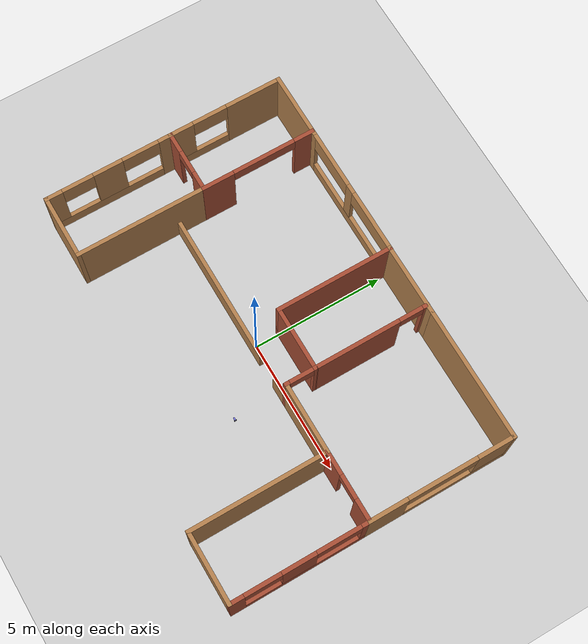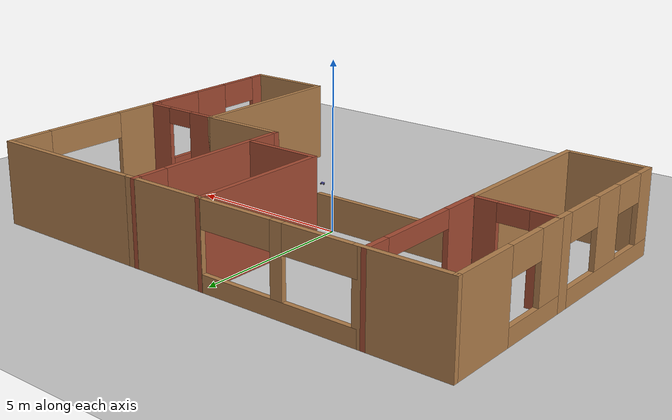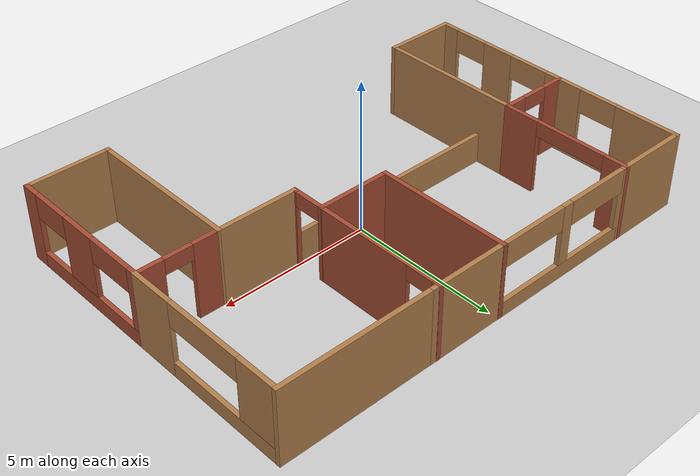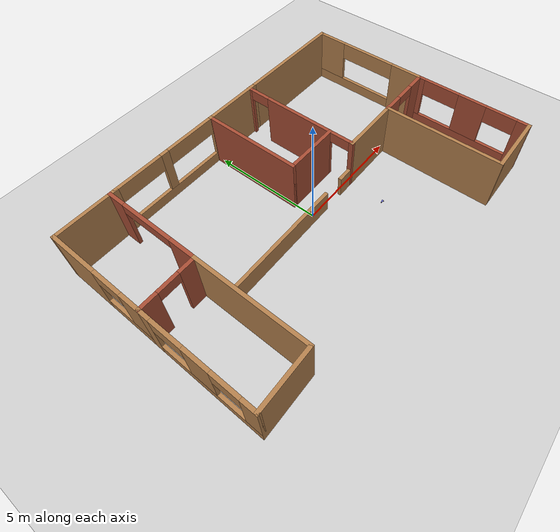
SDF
<?xml version="1.0"?>
<sdf version="1.6">
    <world name="house_diff_drive">
        <scene>
            <ambient>1.0 1.0 1.0</ambient>
            <background>0.8 0.8 0.8</background>
        </scene>

        <plugin
            filename="gz-sim-physics-system"
            name="gz::sim::systems::Physics"></plugin>
        <plugin
            filename="gz-sim-user-commands-system"
            name="gz::sim::systems::UserCommands"></plugin>
        <plugin
            filename="gz-sim-scene-broadcaster-system"
            name="gz::sim::systems::SceneBroadcaster"></plugin>
        <plugin
            filename="libgz-sim-sensors-system.so"
            name="gz::sim::systems::Sensors">
            <render_engine>ogre2</render_engine>
        </plugin>
        <plugin filename="libignition-gazebo-imu-system.so"
            name="ignition::gazebo::systems::Imu"></plugin>

        <light type="directional" name="sun">
            <cast_shadows>true</cast_shadows>
            <pose>0 0 10 0 0 0</pose>
            <diffuse>0.8 0.8 0.8 1</diffuse>
            <specular>0.2 0.2 0.2 1</specular>
            <attenuation>
                <range>1000</range>
                <constant>0.9</constant>
                <linear>0.01</linear>
                <quadratic>0.001</quadratic>
            </attenuation>
            <direction>-0.5 0.1 -0.9</direction>
        </light>

        <model name="ground_plane">
            <static>true</static>
            <link name="link">
                <collision name="collision">
                    <geometry>
                        <plane>
                            <normal>0.0 0.0 1</normal>
                        </plane>
                    </geometry>
                </collision>
                <visual name="visual">
                    <geometry>
                        <plane>
                            <normal>0.0 0.0 1</normal>
                            <size>100 100</size>
                        </plane>
                    </geometry>
                    <material>
                        <ambient>0.8 0.8 0.8 1</ambient>
                        <diffuse>0.8 0.8 0.8 1</diffuse>
                        <specular>0.8 0.8 0.8 1</specular>
                    </material>
                </visual>
            </link>
        </model>

        <model name="turtlebot3_house">
            <static>1</static>
            <include>
                <uri>model://turtlebot3_house</uri>
            </include>
        </model>

        <include>
            <name>vehicle_blue</name>
            <pose>2 -2 0.5 0 0 0</pose>
            <uri>model://vehicle</uri>
        </include>

    </world>
</sdf>

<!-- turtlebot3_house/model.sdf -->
<sdf version='1.6'>
  <model name='turtlebot3_house'>
    <link name='Wall_101'>
      <pose frame=''>-0.05 3.1 0 0 0 -1.5708</pose>
      <self_collide>0</self_collide>
      <kinematic>0</kinematic>
      <visual name='Wall_101_Visual'>
        <pose frame=''>0 0 1.25 0 -0 0</pose>
        <geometry>
          <box>
            <size>4.5 0.15 2.5</size>
          </box>
        </geometry>
        <material>
          <script>
            <uri>file://media/materials/scripts/gazebo.material</uri>
            <name>Gazebo/Bricks</name>
          </script>
          <ambient>1 1 1 1</ambient>
          <diffuse>1 1 1 1</diffuse>
          <specular>0.2 0.2 0.2 1</specular>
          <emissive>0 0 0 1</emissive>
        </material>
        <cast_shadows>1</cast_shadows>
        <transparency>0</transparency>
      </visual>
      <collision name='Wall_101_Collision'>
        <laser_retro>0</laser_retro>
        <max_contacts>10</max_contacts>
        <pose frame=''>0 0 1.25 0 -0 0</pose>
        <geometry>
          <box>
            <size>4.5 0.15 2.5</size>
          </box>
        </geometry>
        <surface>
          <friction>
            <ode>
              <mu>1</mu>
              <mu2>1</mu2>
              <fdir1>0 0 0</fdir1>
              <slip1>0</slip1>
              <slip2>0</slip2>
            </ode>
            <torsional>
              <coefficient>1</coefficient>
              <patch_radius>0</patch_radius>
              <surface_radius>0</surface_radius>
              <use_patch_radius>1</use_patch_radius>
              <ode>
                <slip>0</slip>
              </ode>
            </torsional>
          </friction>
          <bounce>
            <restitution_coefficient>0</restitution_coefficient>
            <threshold>1e+06</threshold>
          </bounce>
          <contact>
            <collide_without_contact>0</collide_without_contact>
            <collide_without_contact_bitmask>1</collide_without_contact_bitmask>
            <collide_bitmask>1</collide_bitmask>
            <ode>
              <soft_cfm>0</soft_cfm>
              <soft_erp>0.2</soft_erp>
              <kp>1e+13</kp>
              <kd>1</kd>
              <max_vel>0.01</max_vel>
              <min_depth>0</min_depth>
            </ode>
            <bullet>
              <split_impulse>1</split_impulse>
              <split_impulse_penetration_threshold>-0.01</split_impulse_penetration_threshold>
              <soft_cfm>0</soft_cfm>
              <soft_erp>0.2</soft_erp>
              <kp>1e+13</kp>
              <kd>1</kd>
            </bullet>
          </contact>
        </surface>
      </collision>
    </link>
    <link name='Wall_104'>
      <pose frame=''>2.3 3.1 0 0 -0 1.5708</pose>
      <self_collide>0</self_collide>
      <kinematic>0</kinematic>
      <visual name='Wall_104_Visual_1'>
        <pose frame=''>2.11625 0 1.25 0 -0 0</pose>
        <geometry>
          <box>
            <size>0.267504 0.15 2.5</size>
          </box>
        </geometry>
        <material>
          <script>
            <uri>file://media/materials/scripts/gazebo.material</uri>
            <name>Gazebo/Bricks</name>
          </script>
          <ambient>1 1 1 1</ambient>
          <diffuse>1 1 1 1</diffuse>
          <specular>0.2 0.2 0.2 1</specular>
          <emissive>0 0 0 1</emissive>
        </material>
        <cast_shadows>1</cast_shadows>
        <transparency>0</transparency>
      </visual>
      <visual name='Wall_104_Visual_2'>
        <pose frame=''>1.5325 0 2.25 0 -0 0</pose>
        <geometry>
          <box>
            <size>0.9 0.15 0.5</size>
          </box>
        </geometry>
        <material>
          <script>
            <uri>file://media/materials/scripts/gazebo.material</uri>
            <name>Gazebo/Bricks</name>
          </script>
          <ambient>1 1 1 1</ambient>
          <diffuse>1 1 1 1</diffuse>
          <specular>0.2 0.2 0.2 1</specular>
          <emissive>0 0 0 1</emissive>
        </material>
        <cast_shadows>1</cast_shadows>
        <transparency>0</transparency>
      </visual>
      <visual name='Wall_104_Visual_0'>
        <pose frame=''>-0.583752 0 1.25 0 -0 0</pose>
        <geometry>
          <box>
            <size>3.3325 0.15 2.5</size>
          </box>
        </geometry>
        <material>
          <script>
            <uri>file://media/materials/scripts/gazebo.material</uri>
            <name>Gazebo/Bricks</name>
          </script>
          <ambient>1 1 1 1</ambient>
          <diffuse>1 1 1 1</diffuse>
          <specular>0.2 0.2 0.2 1</specular>
          <emissive>0 0 0 1</emissive>
        </material>
        <cast_shadows>1</cast_shadows>
        <transparency>0</transparency>
      </visual>
      <collision name='Wall_104_Collision_1'>
        <laser_retro>0</laser_retro>
        <max_contacts>10</max_contacts>
        <pose frame=''>2.11625 0 1.25 0 -0 0</pose>
        <geometry>
          <box>
            <size>0.267504 0.15 2.5</size>
          </box>
        </geometry>
        <surface>
          <friction>
            <ode>
              <mu>1</mu>
              <mu2>1</mu2>
              <fdir1>0 0 0</fdir1>
              <slip1>0</slip1>
              <slip2>0</slip2>
            </ode>
            <torsional>
              <coefficient>1</coefficient>
              <patch_radius>0</patch_radius>
              <surface_radius>0</surface_radius>
              <use_patch_radius>1</use_patch_radius>
              <ode>
                <slip>0</slip>
              </ode>
            </torsional>
          </friction>
          <bounce>
            <restitution_coefficient>0</restitution_coefficient>
            <threshold>1e+06</threshold>
          </bounce>
          <contact>
            <collide_without_contact>0</collide_without_contact>
            <collide_without_contact_bitmask>1</collide_without_contact_bitmask>
            <collide_bitmask>1</collide_bitmask>
            <ode>
              <soft_cfm>0</soft_cfm>
              <soft_erp>0.2</soft_erp>
              <kp>1e+13</kp>
              <kd>1</kd>
              <max_vel>0.01</max_vel>
              <min_depth>0</min_depth>
            </ode>
            <bullet>
              <split_impulse>1</split_impulse>
              <split_impulse_penetration_threshold>-0.01</split_impulse_penetration_threshold>
              <soft_cfm>0</soft_cfm>
              <soft_erp>0.2</soft_erp>
              <kp>1e+13</kp>
              <kd>1</kd>
            </bullet>
          </contact>
        </surface>
      </collision>
      <collision name='Wall_104_Collision_2'>
        <laser_retro>0</laser_retro>
        <max_contacts>10</max_contacts>
        <pose frame=''>1.5325 0 2.25 0 -0 0</pose>
        <geometry>
          <box>
            <size>0.9 0.15 0.5</size>
          </box>
        </geometry>
        <surface>
          <friction>
            <ode>
              <mu>1</mu>
              <mu2>1</mu2>
              <fdir1>0 0 0</fdir1>
              <slip1>0</slip1>
              <slip2>0</slip2>
            </ode>
            <torsional>
              <coefficient>1</coefficient>
              <patch_radius>0</patch_radius>
              <surface_radius>0</surface_radius>
              <use_patch_radius>1</use_patch_radius>
              <ode>
                <slip>0</slip>
              </ode>
            </torsional>
          </friction>
          <bounce>
            <restitution_coefficient>0</restitution_coefficient>
            <threshold>1e+06</threshold>
          </bounce>
          <contact>
            <collide_without_contact>0</collide_without_contact>
            <collide_without_contact_bitmask>1</collide_without_contact_bitmask>
            <collide_bitmask>1</collide_bitmask>
            <ode>
              <soft_cfm>0</soft_cfm>
              <soft_erp>0.2</soft_erp>
              <kp>1e+13</kp>
              <kd>1</kd>
              <max_vel>0.01</max_vel>
              <min_depth>0</min_depth>
            </ode>
            <bullet>
              <split_impulse>1</split_impulse>
              <split_impulse_penetration_threshold>-0.01</split_impulse_penetration_threshold>
              <soft_cfm>0</soft_cfm>
              <soft_erp>0.2</soft_erp>
              <kp>1e+13</kp>
              <kd>1</kd>
            </bullet>
          </contact>
        </surface>
      </collision>
      <collision name='Wall_104_Collision_0'>
        <laser_retro>0</laser_retro>
        <max_contacts>10</max_contacts>
        <pose frame=''>-0.583752 0 1.25 0 -0 0</pose>
        <geometry>
          <box>
            <size>3.3325 0.15 2.5</size>
          </box>
        </geometry>
        <surface>
          <friction>
            <ode>
              <mu>1</mu>
              <mu2>1</mu2>
              <fdir1>0 0 0</fdir1>
              <slip1>0</slip1>
              <slip2>0</slip2>
            </ode>
            <torsional>
              <coefficient>1</coefficient>
              <patch_radius>0</patch_radius>
              <surface_radius>0</surface_radius>
              <use_patch_radius>1</use_patch_radius>
              <ode>
                <slip>0</slip>
              </ode>
            </torsional>
          </friction>
          <bounce>
            <restitution_coefficient>0</restitution_coefficient>
            <threshold>1e+06</threshold>
          </bounce>
          <contact>
            <collide_without_contact>0</collide_without_contact>
            <collide_without_contact_bitmask>1</collide_without_contact_bitmask>
            <collide_bitmask>1</collide_bitmask>
            <ode>
              <soft_cfm>0</soft_cfm>
              <soft_erp>0.2</soft_erp>
              <kp>1e+13</kp>
              <kd>1</kd>
              <max_vel>0.01</max_vel>
              <min_depth>0</min_depth>
            </ode>
            <bullet>
              <split_impulse>1</split_impulse>
              <split_impulse_penetration_threshold>-0.01</split_impulse_penetration_threshold>
              <soft_cfm>0</soft_cfm>
              <soft_erp>0.2</soft_erp>
              <kp>1e+13</kp>
              <kd>1</kd>
            </bullet>
          </contact>
        </surface>
      </collision>
    </link>
    <link name='Wall_106'>
      <pose frame=''>6.2 -0.175 0 0 -0 0</pose>
      <self_collide>0</self_collide>
      <kinematic>0</kinematic>
      <visual name='Wall_106_Visual_1'>
        <pose frame=''>0.922235 0 1.25 0 -0 0</pose>
        <geometry>
          <box>
            <size>0.905529 0.15 2.5</size>
          </box>
        </geometry>
        <material>
          <script>
            <uri>file://media/materials/scripts/gazebo.material</uri>
            <name>Gazebo/Bricks</name>
          </script>
          <ambient>1 1 1 1</ambient>
          <diffuse>1 1 1 1</diffuse>
          <specular>0.2 0.2 0.2 1</specular>
          <emissive>0 0 0 1</emissive>
        </material>
        <cast_shadows>1</cast_shadows>
        <transparency>0</transparency>
      </visual>
      <visual name='Wall_106_Visual_2'>
        <pose frame=''>0.019471 0 2.25 0 -0 0</pose>
        <geometry>
          <box>
            <size>0.9 0.15 0.5</size>
          </box>
        </geometry>
        <material>
          <script>
            <uri>file://media/materials/scripts/gazebo.material</uri>
            <name>Gazebo/Bricks</name>
          </script>
          <ambient>1 1 1 1</ambient>
          <diffuse>1 1 1 1</diffuse>
          <specular>0.2 0.2 0.2 1</specular>
          <emissive>0 0 0 1</emissive>
        </material>
        <cast_shadows>1</cast_shadows>
        <transparency>0</transparency>
      </visual>
      <visual name='Wall_106_Visual_0'>
        <pose frame=''>-0.902765 0 1.25 0 -0 0</pose>
        <geometry>
          <box>
            <size>0.944471 0.15 2.5</size>
          </box>
        </geometry>
        <material>
          <script>
            <uri>file://media/materials/scripts/gazebo.material</uri>
            <name>Gazebo/Bricks</name>
          </script>
          <ambient>1 1 1 1</ambient>
          <diffuse>1 1 1 1</diffuse>
          <specular>0.2 0.2 0.2 1</specular>
          <emissive>0 0 0 1</emissive>
        </material>
        <cast_shadows>1</cast_shadows>
        <transparency>0</transparency>
      </visual>
      <collision name='Wall_106_Collision_1'>
        <laser_retro>0</laser_retro>
        <max_contacts>10</max_contacts>
        <pose frame=''>0.922235 0 1.25 0 -0 0</pose>
        <geometry>
          <box>
            <size>0.905529 0.15 2.5</size>
          </box>
        </geometry>
        <surface>
          <friction>
            <ode>
              <mu>1</mu>
              <mu2>1</mu2>
              <fdir1>0 0 0</fdir1>
              <slip1>0</slip1>
              <slip2>0</slip2>
            </ode>
            <torsional>
              <coefficient>1</coefficient>
              <patch_radius>0</patch_radius>
              <surface_radius>0</surface_radius>
              <use_patch_radius>1</use_patch_radius>
              <ode>
                <slip>0</slip>
              </ode>
            </torsional>
          </friction>
          <bounce>
            <restitution_coefficient>0</restitution_coefficient>
            <threshold>1e+06</threshold>
          </bounce>
          <contact>
            <collide_without_contact>0</collide_without_contact>
            <collide_without_contact_bitmask>1</collide_without_contact_bitmask>
            <collide_bitmask>1</collide_bitmask>
            <ode>
              <soft_cfm>0</soft_cfm>
              <soft_erp>0.2</soft_erp>
              <kp>1e+13</kp>
              <kd>1</kd>
              <max_vel>0.01</max_vel>
              <min_depth>0</min_depth>
            </ode>
            <bullet>
              <split_impulse>1</split_impulse>
              <split_impulse_penetration_threshold>-0.01</split_impulse_penetration_threshold>
              <soft_cfm>0</soft_cfm>
              <soft_erp>0.2</soft_erp>
              <kp>1e+13</kp>
              <kd>1</kd>
            </bullet>
          </contact>
        </surface>
      </collision>
      <collision name='Wall_106_Collision_0'>
        <laser_retro>0</laser_retro>
        <max_contacts>10</max_contacts>
        <pose frame=''>-0.902765 0 1.25 0 -0 0</pose>
        <geometry>
          <box>
            <size>0.944471 0.15 2.5</size>
          </box>
        </geometry>
        <surface>
          <friction>
            <ode>
              <mu>1</mu>
              <mu2>1</mu2>
              <fdir1>0 0 0</fdir1>
              <slip1>0</slip1>
              <slip2>0</slip2>
            </ode>
            <torsional>
              <coefficient>1</coefficient>
              <patch_radius>0</patch_radius>
              <surface_radius>0</surface_radius>
              <use_patch_radius>1</use_patch_radius>
              <ode>
                <slip>0</slip>
              </ode>
            </torsional>
          </friction>
          <bounce>
            <restitution_coefficient>0</restitution_coefficient>
            <threshold>1e+06</threshold>
          </bounce>
          <contact>
            <collide_without_contact>0</collide_without_contact>
            <collide_without_contact_bitmask>1</collide_without_contact_bitmask>
            <collide_bitmask>1</collide_bitmask>
            <ode>
              <soft_cfm>0</soft_cfm>
              <soft_erp>0.2</soft_erp>
              <kp>1e+13</kp>
              <kd>1</kd>
              <max_vel>0.01</max_vel>
              <min_depth>0</min_depth>
            </ode>
            <bullet>
              <split_impulse>1</split_impulse>
              <split_impulse_penetration_threshold>-0.01</split_impulse_penetration_threshold>
              <soft_cfm>0</soft_cfm>
              <soft_erp>0.2</soft_erp>
              <kp>1e+13</kp>
              <kd>1</kd>
            </bullet>
          </contact>
        </surface>
      </collision>
      <collision name='Wall_106_Collision_2'>
        <laser_retro>0</laser_retro>
        <max_contacts>10</max_contacts>
        <pose frame=''>0.019471 0 2.25 0 -0 0</pose>
        <geometry>
          <box>
            <size>0.9 0.15 0.5</size>
          </box>
        </geometry>
        <surface>
          <friction>
            <ode>
              <mu>1</mu>
              <mu2>1</mu2>
              <fdir1>0 0 0</fdir1>
              <slip1>0</slip1>
              <slip2>0</slip2>
            </ode>
            <torsional>
              <coefficient>1</coefficient>
              <patch_radius>0</patch_radius>
              <surface_radius>0</surface_radius>
              <use_patch_radius>1</use_patch_radius>
              <ode>
                <slip>0</slip>
              </ode>
            </torsional>
          </friction>
          <bounce>
            <restitution_coefficient>0</restitution_coefficient>
            <threshold>1e+06</threshold>
          </bounce>
          <contact>
            <collide_without_contact>0</collide_without_contact>
            <collide_without_contact_bitmask>1</collide_without_contact_bitmask>
            <collide_bitmask>1</collide_bitmask>
            <ode>
              <soft_cfm>0</soft_cfm>
              <soft_erp>0.2</soft_erp>
              <kp>1e+13</kp>
              <kd>1</kd>
              <max_vel>0.01</max_vel>
              <min_depth>0</min_depth>
            </ode>
            <bullet>
              <split_impulse>1</split_impulse>
              <split_impulse_penetration_threshold>-0.01</split_impulse_penetration_threshold>
              <soft_cfm>0</soft_cfm>
              <soft_erp>0.2</soft_erp>
              <kp>1e+13</kp>
              <kd>1</kd>
            </bullet>
          </contact>
        </surface>
      </collision>
    </link>
    <link name='Wall_108'>
      <pose frame=''>-1.37512 -0.17488 0 0 -0 0</pose>
      <self_collide>0</self_collide>
      <kinematic>0</kinematic>
      <visual name='Wall_108_Visual_0'>
        <pose frame=''>-0.856324 0 0.5 0 -0 0</pose>
        <geometry>
          <box>
            <size>5.78735 0.15 1</size>
          </box>
        </geometry>
        <material>
          <script>
            <uri>file://media/materials/scripts/gazebo.material</uri>
            <name>Gazebo/Wood</name>
          </script>
          <ambient>1 1 1 1</ambient>
          <diffuse>1 1 1 1</diffuse>
          <specular>0.2 0.2 0.2 1</specular>
          <emissive>0 0 0 1</emissive>
        </material>
        <cast_shadows>1</cast_shadows>
        <transparency>0</transparency>
      </visual>
      <visual name='Wall_108_Visual_1'>
        <pose frame=''>3.34368 0 0.5 0 -0 0</pose>
        <geometry>
          <box>
            <size>0.812647 0.15 1</size>
          </box>
        </geometry>
        <material>
          <script>
            <uri>file://media/materials/scripts/gazebo.material</uri>
            <name>Gazebo/Wood</name>
          </script>
          <ambient>1 1 1 1</ambient>
          <diffuse>1 1 1 1</diffuse>
          <specular>0.2 0.2 0.2 1</specular>
          <emissive>0 0 0 1</emissive>
        </material>
        <cast_shadows>1</cast_shadows>
        <transparency>0</transparency>
      </visual>
      <collision name='Wall_108_Collision_1'>
        <laser_retro>0</laser_retro>
        <max_contacts>10</max_contacts>
        <pose frame=''>3.34368 0 0.5 0 -0 0</pose>
        <geometry>
          <box>
            <size>0.812647 0.15 1</size>
          </box>
        </geometry>
        <surface>
          <friction>
            <ode>
              <mu>1</mu>
              <mu2>1</mu2>
              <fdir1>0 0 0</fdir1>
              <slip1>0</slip1>
              <slip2>0</slip2>
            </ode>
            <torsional>
              <coefficient>1</coefficient>
              <patch_radius>0</patch_radius>
              <surface_radius>0</surface_radius>
              <use_patch_radius>1</use_patch_radius>
              <ode>
                <slip>0</slip>
              </ode>
            </torsional>
          </friction>
          <bounce>
            <restitution_coefficient>0</restitution_coefficient>
            <threshold>1e+06</threshold>
          </bounce>
          <contact>
            <collide_without_contact>0</collide_without_contact>
            <collide_without_contact_bitmask>1</collide_without_contact_bitmask>
            <collide_bitmask>1</collide_bitmask>
            <ode>
              <soft_cfm>0</soft_cfm>
              <soft_erp>0.2</soft_erp>
              <kp>1e+13</kp>
              <kd>1</kd>
              <max_vel>0.01</max_vel>
              <min_depth>0</min_depth>
            </ode>
            <bullet>
              <split_impulse>1</split_impulse>
              <split_impulse_penetration_threshold>-0.01</split_impulse_penetration_threshold>
              <soft_cfm>0</soft_cfm>
              <soft_erp>0.2</soft_erp>
              <kp>1e+13</kp>
              <kd>1</kd>
            </bullet>
          </contact>
        </surface>
      </collision>
      <collision name='Wall_108_Collision_0'>
        <laser_retro>0</laser_retro>
        <max_contacts>10</max_contacts>
        <pose frame=''>-0.856324 0 0.5 0 -0 0</pose>
        <geometry>
          <box>
            <size>5.78735 0.15 1</size>
          </box>
        </geometry>
        <surface>
          <friction>
            <ode>
              <mu>1</mu>
              <mu2>1</mu2>
              <fdir1>0 0 0</fdir1>
              <slip1>0</slip1>
              <slip2>0</slip2>
            </ode>
            <torsional>
              <coefficient>1</coefficient>
              <patch_radius>0</patch_radius>
              <surface_radius>0</surface_radius>
              <use_patch_radius>1</use_patch_radius>
              <ode>
                <slip>0</slip>
              </ode>
            </torsional>
          </friction>
          <bounce>
            <restitution_coefficient>0</restitution_coefficient>
            <threshold>1e+06</threshold>
          </bounce>
          <contact>
            <collide_without_contact>0</collide_without_contact>
            <collide_without_contact_bitmask>1</collide_without_contact_bitmask>
            <collide_bitmask>1</collide_bitmask>
            <ode>
              <soft_cfm>0</soft_cfm>
              <soft_erp>0.2</soft_erp>
              <kp>1e+13</kp>
              <kd>1</kd>
              <max_vel>0.01</max_vel>
              <min_depth>0</min_depth>
            </ode>
            <bullet>
              <split_impulse>1</split_impulse>
              <split_impulse_penetration_threshold>-0.01</split_impulse_penetration_threshold>
              <soft_cfm>0</soft_cfm>
              <soft_erp>0.2</soft_erp>
              <kp>1e+13</kp>
              <kd>1</kd>
            </bullet>
          </contact>
        </surface>
      </collision>
    </link>
    <link name='Wall_81'>
      <pose frame=''>5.07752 5.2688 0 0 -0 3.14159</pose>
      <self_collide>0</self_collide>
      <kinematic>0</kinematic>
      <visual name='Wall_81_Visual'>
        <pose frame=''>0 0 1.25 0 -0 0</pose>
        <geometry>
          <box>
            <size>5 0.15 2.5</size>
          </box>
        </geometry>
        <material>
          <script>
            <uri>file://media/materials/scripts/gazebo.material</uri>
            <name>Gazebo/Wood</name>
          </script>
          <ambient>1 1 1 1</ambient>
          <diffuse>1 1 1 1</diffuse>
          <specular>0.2 0.2 0.2 1</specular>
          <emissive>0 0 0 1</emissive>
        </material>
        <cast_shadows>1</cast_shadows>
        <transparency>0</transparency>
      </visual>
      <collision name='Wall_81_Collision'>
        <laser_retro>0</laser_retro>
        <max_contacts>10</max_contacts>
        <pose frame=''>0 0 1.25 0 -0 0</pose>
        <geometry>
          <box>
            <size>5 0.15 2.5</size>
          </box>
        </geometry>
        <surface>
          <friction>
            <ode>
              <mu>1</mu>
              <mu2>1</mu2>
              <fdir1>0 0 0</fdir1>
              <slip1>0</slip1>
              <slip2>0</slip2>
            </ode>
            <torsional>
              <coefficient>1</coefficient>
              <patch_radius>0</patch_radius>
              <surface_radius>0</surface_radius>
              <use_patch_radius>1</use_patch_radius>
              <ode>
                <slip>0</slip>
              </ode>
            </torsional>
          </friction>
          <bounce>
            <restitution_coefficient>0</restitution_coefficient>
            <threshold>1e+06</threshold>
          </bounce>
          <contact>
            <collide_without_contact>0</collide_without_contact>
            <collide_without_contact_bitmask>1</collide_without_contact_bitmask>
            <collide_bitmask>1</collide_bitmask>
            <ode>
              <soft_cfm>0</soft_cfm>
              <soft_erp>0.2</soft_erp>
              <kp>1e+13</kp>
              <kd>1</kd>
              <max_vel>0.01</max_vel>
              <min_depth>0</min_depth>
            </ode>
            <bullet>
              <split_impulse>1</split_impulse>
              <split_impulse_penetration_threshold>-0.01</split_impulse_penetration_threshold>
              <soft_cfm>0</soft_cfm>
              <soft_erp>0.2</soft_erp>
              <kp>1e+13</kp>
              <kd>1</kd>
            </bullet>
          </contact>
        </surface>
      </collision>
    </link>
    <link name='Wall_82'>
      <pose frame=''>1.25 5.26876 0 0 -0 3.14159</pose>
      <self_collide>0</self_collide>
      <kinematic>0</kinematic>
      <visual name='Wall_82_Visual'>
        <pose frame=''>0 0 1.25 0 -0 0</pose>
        <geometry>
          <box>
            <size>2.75 0.15 2.5</size>
          </box>
        </geometry>
        <material>
          <script>
            <uri>file://media/materials/scripts/gazebo.material</uri>
            <name>Gazebo/Wood</name>
          </script>
          <ambient>1 1 1 1</ambient>
          <diffuse>1 1 1 1</diffuse>
          <specular>0.2 0.2 0.2 1</specular>
          <emissive>0 0 0 1</emissive>
        </material>
        <cast_shadows>1</cast_shadows>
        <transparency>0</transparency>
      </visual>
      <collision name='Wall_82_Collision'>
        <laser_retro>0</laser_retro>
        <max_contacts>10</max_contacts>
        <pose frame=''>0 0 1.25 0 -0 0</pose>
        <geometry>
          <box>
            <size>2.75 0.15 2.5</size>
          </box>
        </geometry>
        <surface>
          <friction>
            <ode>
              <mu>1</mu>
              <mu2>1</mu2>
              <fdir1>0 0 0</fdir1>
              <slip1>0</slip1>
              <slip2>0</slip2>
            </ode>
            <torsional>
              <coefficient>1</coefficient>
              <patch_radius>0</patch_radius>
              <surface_radius>0</surface_radius>
              <use_patch_radius>1</use_patch_radius>
              <ode>
                <slip>0</slip>
              </ode>
            </torsional>
          </friction>
          <bounce>
            <restitution_coefficient>0</restitution_coefficient>
            <threshold>1e+06</threshold>
          </bounce>
          <contact>
            <collide_without_contact>0</collide_without_contact>
            <collide_without_contact_bitmask>1</collide_without_contact_bitmask>
            <collide_bitmask>1</collide_bitmask>
            <ode>
              <soft_cfm>0</soft_cfm>
              <soft_erp>0.2</soft_erp>
              <kp>1e+13</kp>
              <kd>1</kd>
              <max_vel>0.01</max_vel>
              <min_depth>0</min_depth>
            </ode>
            <bullet>
              <split_impulse>1</split_impulse>
              <split_impulse_penetration_threshold>-0.01</split_impulse_penetration_threshold>
              <soft_cfm>0</soft_cfm>
              <soft_erp>0.2</soft_erp>
              <kp>1e+13</kp>
              <kd>1</kd>
            </bullet>
          </contact>
        </surface>
      </collision>
    </link>
    <link name='Wall_83'>
      <pose frame=''>-2.475 5.275 0 0 -0 3.14159</pose>
      <self_collide>0</self_collide>
      <kinematic>0</kinematic>
      <visual name='Wall_83_Visual_2'>
        <pose frame=''>0.110246 0 1.5 0 -0 0</pose>
        <geometry>
          <box>
            <size>0.37052 0.15 2</size>
          </box>
        </geometry>
        <material>
          <script>
            <uri>file://media/materials/scripts/gazebo.material</uri>
            <name>Gazebo/Wood</name>
          </script>
          <ambient>1 1 1 1</ambient>
          <diffuse>1 1 1 1</diffuse>
          <specular>0.2 0.2 0.2 1</specular>
          <emissive>0 0 0 1</emissive>
        </material>
        <cast_shadows>1</cast_shadows>
        <transparency>0</transparency>
      </visual>
      <visual name='Wall_83_Visual_6'>
        <pose frame=''>1.39775 0 2.1 0 -0 0</pose>
        <geometry>
          <box>
            <size>2.20449 0.15 0.8</size>
          </box>
        </geometry>
        <material>
          <script>
            <uri>file://media/materials/scripts/gazebo.material</uri>
            <name>Gazebo/Wood</name>
          </script>
          <ambient>1 1 1 1</ambient>
          <diffuse>1 1 1 1</diffuse>
          <specular>0.2 0.2 0.2 1</specular>
          <emissive>0 0 0 1</emissive>
        </material>
        <cast_shadows>1</cast_shadows>
        <transparency>0</transparency>
      </visual>
      <visual name='Wall_83_Visual_3'>
        <pose frame=''>0.110246 0 1.5 0 -0 0</pose>
        <geometry>
          <box>
            <size>0.37052 0.15 2</size>
          </box>
        </geometry>
        <material>
          <script>
            <uri>file://media/materials/scripts/gazebo.material</uri>
            <name>Gazebo/Wood</name>
          </script>
          <ambient>1 1 1 1</ambient>
          <diffuse>1 1 1 1</diffuse>
          <specular>0.2 0.2 0.2 1</specular>
          <emissive>0 0 0 1</emissive>
        </material>
        <cast_shadows>1</cast_shadows>
        <transparency>0</transparency>
      </visual>
      <visual name='Wall_83_Visual_1'>
        <pose frame=''>0.080993 0 0.25 0 -0 0</pose>
        <geometry>
          <box>
            <size>4.83801 0.15 0.5</size>
          </box>
        </geometry>
        <material>
          <script>
            <uri>file://media/materials/scripts/gazebo.material</uri>
            <name>Gazebo/Wood</name>
          </script>
          <ambient>1 1 1 1</ambient>
          <diffuse>1 1 1 1</diffuse>
          <specular>0.2 0.2 0.2 1</specular>
          <emissive>0 0 0 1</emissive>
        </material>
        <cast_shadows>1</cast_shadows>
        <transparency>0</transparency>
      </visual>
      <visual name='Wall_83_Visual_4'>
        <pose frame=''>-1.20651 0 2.1 0 -0 0</pose>
        <geometry>
          <box>
            <size>2.263 0.15 0.8</size>
          </box>
        </geometry>
        <material>
          <script>
            <uri>file://media/materials/scripts/gazebo.material</uri>
            <name>Gazebo/Wood</name>
          </script>
          <ambient>1 1 1 1</ambient>
          <diffuse>1 1 1 1</diffuse>
          <specular>0.2 0.2 0.2 1</specular>
          <emissive>0 0 0 1</emissive>
        </material>
        <cast_shadows>1</cast_shadows>
        <transparency>0</transparency>
      </visual>
      <visual name='Wall_83_Visual_5'>
        <pose frame=''>1.39775 0 2.1 0 -0 0</pose>
        <geometry>
          <box>
            <size>2.20449 0.15 0.8</size>
          </box>
        </geometry>
        <material>
          <script>
            <uri>file://media/materials/scripts/gazebo.material</uri>
            <name>Gazebo/Wood</name>
          </script>
          <ambient>1 1 1 1</ambient>
          <diffuse>1 1 1 1</diffuse>
          <specular>0.2 0.2 0.2 1</specular>
          <emissive>0 0 0 1</emissive>
        </material>
        <cast_shadows>1</cast_shadows>
        <transparency>0</transparency>
      </visual>
      <visual name='Wall_83_Visual_0'>
        <pose frame=''>-2.41901 0 1.25 0 -0 0</pose>
        <geometry>
          <box>
            <size>0.161986 0.15 2.5</size>
          </box>
        </geometry>
        <material>
          <script>
            <uri>file://media/materials/scripts/gazebo.material</uri>
            <name>Gazebo/Wood</name>
          </script>
          <ambient>1 1 1 1</ambient>
          <diffuse>1 1 1 1</diffuse>
          <specular>0.2 0.2 0.2 1</specular>
          <emissive>0 0 0 1</emissive>
        </material>
        <cast_shadows>1</cast_shadows>
        <transparency>0</transparency>
      </visual>
      <collision name='Wall_83_Collision_4'>
        <laser_retro>0</laser_retro>
        <max_contacts>10</max_contacts>
        <pose frame=''>-1.20651 0 2.1 0 -0 0</pose>
        <geometry>
          <box>
            <size>2.263 0.15 0.8</size>
          </box>
        </geometry>
        <surface>
          <friction>
            <ode>
              <mu>1</mu>
              <mu2>1</mu2>
              <fdir1>0 0 0</fdir1>
              <slip1>0</slip1>
              <slip2>0</slip2>
            </ode>
            <torsional>
              <coefficient>1</coefficient>
              <patch_radius>0</patch_radius>
              <surface_radius>0</surface_radius>
              <use_patch_radius>1</use_patch_radius>
              <ode>
                <slip>0</slip>
              </ode>
            </torsional>
          </friction>
          <bounce>
            <restitution_coefficient>0</restitution_coefficient>
            <threshold>1e+06</threshold>
          </bounce>
          <contact>
            <collide_without_contact>0</collide_without_contact>
            <collide_without_contact_bitmask>1</collide_without_contact_bitmask>
            <collide_bitmask>1</collide_bitmask>
            <ode>
              <soft_cfm>0</soft_cfm>
              <soft_erp>0.2</soft_erp>
              <kp>1e+13</kp>
              <kd>1</kd>
              <max_vel>0.01</max_vel>
              <min_depth>0</min_depth>
            </ode>
            <bullet>
              <split_impulse>1</split_impulse>
              <split_impulse_penetration_threshold>-0.01</split_impulse_penetration_threshold>
              <soft_cfm>0</soft_cfm>
              <soft_erp>0.2</soft_erp>
              <kp>1e+13</kp>
              <kd>1</kd>
            </bullet>
          </contact>
        </surface>
      </collision>
      <collision name='Wall_83_Collision_2'>
        <laser_retro>0</laser_retro>
        <max_contacts>10</max_contacts>
        <pose frame=''>0.110246 0 1.5 0 -0 0</pose>
        <geometry>
          <box>
            <size>0.37052 0.15 2</size>
          </box>
        </geometry>
        <surface>
          <friction>
            <ode>
              <mu>1</mu>
              <mu2>1</mu2>
              <fdir1>0 0 0</fdir1>
              <slip1>0</slip1>
              <slip2>0</slip2>
            </ode>
            <torsional>
              <coefficient>1</coefficient>
              <patch_radius>0</patch_radius>
              <surface_radius>0</surface_radius>
              <use_patch_radius>1</use_patch_radius>
              <ode>
                <slip>0</slip>
              </ode>
            </torsional>
          </friction>
          <bounce>
            <restitution_coefficient>0</restitution_coefficient>
            <threshold>1e+06</threshold>
          </bounce>
          <contact>
            <collide_without_contact>0</collide_without_contact>
            <collide_without_contact_bitmask>1</collide_without_contact_bitmask>
            <collide_bitmask>1</collide_bitmask>
            <ode>
              <soft_cfm>0</soft_cfm>
              <soft_erp>0.2</soft_erp>
              <kp>1e+13</kp>
              <kd>1</kd>
              <max_vel>0.01</max_vel>
              <min_depth>0</min_depth>
            </ode>
            <bullet>
              <split_impulse>1</split_impulse>
              <split_impulse_penetration_threshold>-0.01</split_impulse_penetration_threshold>
              <soft_cfm>0</soft_cfm>
              <soft_erp>0.2</soft_erp>
              <kp>1e+13</kp>
              <kd>1</kd>
            </bullet>
          </contact>
        </surface>
      </collision>
      <collision name='Wall_83_Collision_6'>
        <laser_retro>0</laser_retro>
        <max_contacts>10</max_contacts>
        <pose frame=''>1.39775 0 2.1 0 -0 0</pose>
        <geometry>
          <box>
            <size>2.20449 0.15 0.8</size>
          </box>
        </geometry>
        <surface>
          <friction>
            <ode>
              <mu>1</mu>
              <mu2>1</mu2>
              <fdir1>0 0 0</fdir1>
              <slip1>0</slip1>
              <slip2>0</slip2>
            </ode>
            <torsional>
              <coefficient>1</coefficient>
              <patch_radius>0</patch_radius>
              <surface_radius>0</surface_radius>
              <use_patch_radius>1</use_patch_radius>
              <ode>
                <slip>0</slip>
              </ode>
            </torsional>
          </friction>
          <bounce>
            <restitution_coefficient>0</restitution_coefficient>
            <threshold>1e+06</threshold>
          </bounce>
          <contact>
            <collide_without_contact>0</collide_without_contact>
            <collide_without_contact_bitmask>1</collide_without_contact_bitmask>
            <collide_bitmask>1</collide_bitmask>
            <ode>
              <soft_cfm>0</soft_cfm>
              <soft_erp>0.2</soft_erp>
              <kp>1e+13</kp>
              <kd>1</kd>
              <max_vel>0.01</max_vel>
              <min_depth>0</min_depth>
            </ode>
            <bullet>
              <split_impulse>1</split_impulse>
              <split_impulse_penetration_threshold>-0.01</split_impulse_penetration_threshold>
              <soft_cfm>0</soft_cfm>
              <soft_erp>0.2</soft_erp>
              <kp>1e+13</kp>
              <kd>1</kd>
            </bullet>
          </contact>
        </surface>
      </collision>
      <collision name='Wall_83_Collision_0'>
        <laser_retro>0</laser_retro>
        <max_contacts>10</max_contacts>
        <pose frame=''>-2.41901 0 1.25 0 -0 0</pose>
        <geometry>
          <box>
            <size>0.161986 0.15 2.5</size>
          </box>
        </geometry>
        <surface>
          <friction>
            <ode>
              <mu>1</mu>
              <mu2>1</mu2>
              <fdir1>0 0 0</fdir1>
              <slip1>0</slip1>
              <slip2>0</slip2>
            </ode>
            <torsional>
              <coefficient>1</coefficient>
              <patch_radius>0</patch_radius>
              <surface_radius>0</surface_radius>
              <use_patch_radius>1</use_patch_radius>
              <ode>
                <slip>0</slip>
              </ode>
            </torsional>
          </friction>
          <bounce>
            <restitution_coefficient>0</restitution_coefficient>
            <threshold>1e+06</threshold>
          </bounce>
          <contact>
            <collide_without_contact>0</collide_without_contact>
            <collide_without_contact_bitmask>1</collide_without_contact_bitmask>
            <collide_bitmask>1</collide_bitmask>
            <ode>
              <soft_cfm>0</soft_cfm>
              <soft_erp>0.2</soft_erp>
              <kp>1e+13</kp>
              <kd>1</kd>
              <max_vel>0.01</max_vel>
              <min_depth>0</min_depth>
            </ode>
            <bullet>
              <split_impulse>1</split_impulse>
              <split_impulse_penetration_threshold>-0.01</split_impulse_penetration_threshold>
              <soft_cfm>0</soft_cfm>
              <soft_erp>0.2</soft_erp>
              <kp>1e+13</kp>
              <kd>1</kd>
            </bullet>
          </contact>
        </surface>
      </collision>
      <collision name='Wall_83_Collision_1'>
        <laser_retro>0</laser_retro>
        <max_contacts>10</max_contacts>
        <pose frame=''>0.080993 0 0.25 0 -0 0</pose>
        <geometry>
          <box>
            <size>4.83801 0.15 0.5</size>
          </box>
        </geometry>
        <surface>
          <friction>
            <ode>
              <mu>1</mu>
              <mu2>1</mu2>
              <fdir1>0 0 0</fdir1>
              <slip1>0</slip1>
              <slip2>0</slip2>
            </ode>
            <torsional>
              <coefficient>1</coefficient>
              <patch_radius>0</patch_radius>
              <surface_radius>0</surface_radius>
              <use_patch_radius>1</use_patch_radius>
              <ode>
                <slip>0</slip>
              </ode>
            </torsional>
          </friction>
          <bounce>
            <restitution_coefficient>0</restitution_coefficient>
            <threshold>1e+06</threshold>
          </bounce>
          <contact>
            <collide_without_contact>0</collide_without_contact>
            <collide_without_contact_bitmask>1</collide_without_contact_bitmask>
            <collide_bitmask>1</collide_bitmask>
            <ode>
              <soft_cfm>0</soft_cfm>
              <soft_erp>0.2</soft_erp>
              <kp>1e+13</kp>
              <kd>1</kd>
              <max_vel>0.01</max_vel>
              <min_depth>0</min_depth>
            </ode>
            <bullet>
              <split_impulse>1</split_impulse>
              <split_impulse_penetration_threshold>-0.01</split_impulse_penetration_threshold>
              <soft_cfm>0</soft_cfm>
              <soft_erp>0.2</soft_erp>
              <kp>1e+13</kp>
              <kd>1</kd>
            </bullet>
          </contact>
        </surface>
      </collision>
      <collision name='Wall_83_Collision_3'>
        <laser_retro>0</laser_retro>
        <max_contacts>10</max_contacts>
        <pose frame=''>0.110246 0 1.5 0 -0 0</pose>
        <geometry>
          <box>
            <size>0.37052 0.15 2</size>
          </box>
        </geometry>
        <surface>
          <friction>
            <ode>
              <mu>1</mu>
              <mu2>1</mu2>
              <fdir1>0 0 0</fdir1>
              <slip1>0</slip1>
              <slip2>0</slip2>
            </ode>
            <torsional>
              <coefficient>1</coefficient>
              <patch_radius>0</patch_radius>
              <surface_radius>0</surface_radius>
              <use_patch_radius>1</use_patch_radius>
              <ode>
                <slip>0</slip>
              </ode>
            </torsional>
          </friction>
          <bounce>
            <restitution_coefficient>0</restitution_coefficient>
            <threshold>1e+06</threshold>
          </bounce>
          <contact>
            <collide_without_contact>0</collide_without_contact>
            <collide_without_contact_bitmask>1</collide_without_contact_bitmask>
            <collide_bitmask>1</collide_bitmask>
            <ode>
              <soft_cfm>0</soft_cfm>
              <soft_erp>0.2</soft_erp>
              <kp>1e+13</kp>
              <kd>1</kd>
              <max_vel>0.01</max_vel>
              <min_depth>0</min_depth>
            </ode>
            <bullet>
              <split_impulse>1</split_impulse>
              <split_impulse_penetration_threshold>-0.01</split_impulse_penetration_threshold>
              <soft_cfm>0</soft_cfm>
              <soft_erp>0.2</soft_erp>
              <kp>1e+13</kp>
              <kd>1</kd>
            </bullet>
          </contact>
        </surface>
      </collision>
      <collision name='Wall_83_Collision_5'>
        <laser_retro>0</laser_retro>
        <max_contacts>10</max_contacts>
        <pose frame=''>1.39775 0 2.1 0 -0 0</pose>
        <geometry>
          <box>
            <size>2.20449 0.15 0.8</size>
          </box>
        </geometry>
        <surface>
          <friction>
            <ode>
              <mu>1</mu>
              <mu2>1</mu2>
              <fdir1>0 0 0</fdir1>
              <slip1>0</slip1>
              <slip2>0</slip2>
            </ode>
            <torsional>
              <coefficient>1</coefficient>
              <patch_radius>0</patch_radius>
              <surface_radius>0</surface_radius>
              <use_patch_radius>1</use_patch_radius>
              <ode>
                <slip>0</slip>
              </ode>
            </torsional>
          </friction>
          <bounce>
            <restitution_coefficient>0</restitution_coefficient>
            <threshold>1e+06</threshold>
          </bounce>
          <contact>
            <collide_without_contact>0</collide_without_contact>
            <collide_without_contact_bitmask>1</collide_without_contact_bitmask>
            <collide_bitmask>1</collide_bitmask>
            <ode>
              <soft_cfm>0</soft_cfm>
              <soft_erp>0.2</soft_erp>
              <kp>1e+13</kp>
              <kd>1</kd>
              <max_vel>0.01</max_vel>
              <min_depth>0</min_depth>
            </ode>
            <bullet>
              <split_impulse>1</split_impulse>
              <split_impulse_penetration_threshold>-0.01</split_impulse_penetration_threshold>
              <soft_cfm>0</soft_cfm>
              <soft_erp>0.2</soft_erp>
              <kp>1e+13</kp>
              <kd>1</kd>
            </bullet>
          </contact>
        </surface>
      </collision>
    </link>
    <link name='Wall_84'>
      <pose frame=''>-6.2 5.275 0 0 -0 3.14159</pose>
      <self_collide>0</self_collide>
      <kinematic>0</kinematic>
      <visual name='Wall_84_Visual'>
        <pose frame=''>0 0 1.25 0 -0 0</pose>
        <geometry>
          <box>
            <size>2.75 0.15 2.5</size>
          </box>
        </geometry>
        <material>
          <script>
            <uri>file://media/materials/scripts/gazebo.material</uri>
            <name>Gazebo/Wood</name>
          </script>
          <ambient>1 1 1 1</ambient>
          <diffuse>1 1 1 1</diffuse>
          <specular>0.2 0.2 0.2 1</specular>
          <emissive>0 0 0 1</emissive>
        </material>
        <cast_shadows>1</cast_shadows>
        <transparency>0</transparency>
      </visual>
      <collision name='Wall_84_Collision'>
        <laser_retro>0</laser_retro>
        <max_contacts>10</max_contacts>
        <pose frame=''>0 0 1.25 0 -0 0</pose>
        <geometry>
          <box>
            <size>2.75 0.15 2.5</size>
          </box>
        </geometry>
        <surface>
          <friction>
            <ode>
              <mu>1</mu>
              <mu2>1</mu2>
              <fdir1>0 0 0</fdir1>
              <slip1>0</slip1>
              <slip2>0</slip2>
            </ode>
            <torsional>
              <coefficient>1</coefficient>
              <patch_radius>0</patch_radius>
              <surface_radius>0</surface_radius>
              <use_patch_radius>1</use_patch_radius>
              <ode>
                <slip>0</slip>
              </ode>
            </torsional>
          </friction>
          <bounce>
            <restitution_coefficient>0</restitution_coefficient>
            <threshold>1e+06</threshold>
          </bounce>
          <contact>
            <collide_without_contact>0</collide_without_contact>
            <collide_without_contact_bitmask>1</collide_without_contact_bitmask>
            <collide_bitmask>1</collide_bitmask>
            <ode>
              <soft_cfm>0</soft_cfm>
              <soft_erp>0.2</soft_erp>
              <kp>1e+13</kp>
              <kd>1</kd>
              <max_vel>0.01</max_vel>
              <min_depth>0</min_depth>
            </ode>
            <bullet>
              <split_impulse>1</split_impulse>
              <split_impulse_penetration_threshold>-0.01</split_impulse_penetration_threshold>
              <soft_cfm>0</soft_cfm>
              <soft_erp>0.2</soft_erp>
              <kp>1e+13</kp>
              <kd>1</kd>
            </bullet>
          </contact>
        </surface>
      </collision>
    </link>
    <link name='Wall_85'>
      <pose frame=''>-7.5 3.1 0 0 0 -1.5708</pose>
      <self_collide>0</self_collide>
      <kinematic>0</kinematic>
      <visual name='Wall_85_Visual_3'>
        <pose frame=''>0.62212 0 2.1 0 -0 0</pose>
        <geometry>
          <box>
            <size>1.332 0.15 0.8</size>
          </box>
        </geometry>
        <material>
          <script>
            <uri>file://media/materials/scripts/gazebo.material</uri>
            <name>Gazebo/Wood</name>
          </script>
          <ambient>1 1 1 1</ambient>
          <diffuse>1 1 1 1</diffuse>
          <specular>0.2 0.2 0.2 1</specular>
          <emissive>0 0 0 1</emissive>
        </material>
        <cast_shadows>1</cast_shadows>
        <transparency>0</transparency>
      </visual>
      <visual name='Wall_85_Visual_2'>
        <pose frame=''>1.76906 0 1.5 0 -0 0</pose>
        <geometry>
          <box>
            <size>0.96188 0.15 2</size>
          </box>
        </geometry>
        <material>
          <script>
            <uri>file://media/materials/scripts/gazebo.material</uri>
            <name>Gazebo/Wood</name>
          </script>
          <ambient>1 1 1 1</ambient>
          <diffuse>1 1 1 1</diffuse>
          <specular>0.2 0.2 0.2 1</specular>
          <emissive>0 0 0 1</emissive>
        </material>
        <cast_shadows>1</cast_shadows>
        <transparency>0</transparency>
      </visual>
      <visual name='Wall_85_Visual_0'>
        <pose frame=''>-1.14694 0 1.25 0 -0 0</pose>
        <geometry>
          <box>
            <size>2.20612 0.15 2.5</size>
          </box>
        </geometry>
        <material>
          <script>
            <uri>file://media/materials/scripts/gazebo.material</uri>
            <name>Gazebo/Wood</name>
          </script>
          <ambient>1 1 1 1</ambient>
          <diffuse>1 1 1 1</diffuse>
          <specular>0.2 0.2 0.2 1</specular>
          <emissive>0 0 0 1</emissive>
        </material>
        <cast_shadows>1</cast_shadows>
        <transparency>0</transparency>
      </visual>
      <visual name='Wall_85_Visual_1'>
        <pose frame=''>1.10306 0 0.25 0 -0 0</pose>
        <geometry>
          <box>
            <size>2.29388 0.15 0.5</size>
          </box>
        </geometry>
        <material>
          <script>
            <uri>file://media/materials/scripts/gazebo.material</uri>
            <name>Gazebo/Wood</name>
          </script>
          <ambient>1 1 1 1</ambient>
          <diffuse>1 1 1 1</diffuse>
          <specular>0.2 0.2 0.2 1</specular>
          <emissive>0 0 0 1</emissive>
        </material>
        <cast_shadows>1</cast_shadows>
        <transparency>0</transparency>
      </visual>
      <collision name='Wall_85_Collision_3'>
        <laser_retro>0</laser_retro>
        <max_contacts>10</max_contacts>
        <pose frame=''>0.62212 0 2.1 0 -0 0</pose>
        <geometry>
          <box>
            <size>1.332 0.15 0.8</size>
          </box>
        </geometry>
        <surface>
          <friction>
            <ode>
              <mu>1</mu>
              <mu2>1</mu2>
              <fdir1>0 0 0</fdir1>
              <slip1>0</slip1>
              <slip2>0</slip2>
            </ode>
            <torsional>
              <coefficient>1</coefficient>
              <patch_radius>0</patch_radius>
              <surface_radius>0</surface_radius>
              <use_patch_radius>1</use_patch_radius>
              <ode>
                <slip>0</slip>
              </ode>
            </torsional>
          </friction>
          <bounce>
            <restitution_coefficient>0</restitution_coefficient>
            <threshold>1e+06</threshold>
          </bounce>
          <contact>
            <collide_without_contact>0</collide_without_contact>
            <collide_without_contact_bitmask>1</collide_without_contact_bitmask>
            <collide_bitmask>1</collide_bitmask>
            <ode>
              <soft_cfm>0</soft_cfm>
              <soft_erp>0.2</soft_erp>
              <kp>1e+13</kp>
              <kd>1</kd>
              <max_vel>0.01</max_vel>
              <min_depth>0</min_depth>
            </ode>
            <bullet>
              <split_impulse>1</split_impulse>
              <split_impulse_penetration_threshold>-0.01</split_impulse_penetration_threshold>
              <soft_cfm>0</soft_cfm>
              <soft_erp>0.2</soft_erp>
              <kp>1e+13</kp>
              <kd>1</kd>
            </bullet>
          </contact>
        </surface>
      </collision>
      <collision name='Wall_85_Collision_2'>
        <laser_retro>0</laser_retro>
        <max_contacts>10</max_contacts>
        <pose frame=''>1.76906 0 1.5 0 -0 0</pose>
        <geometry>
          <box>
            <size>0.96188 0.15 2</size>
          </box>
        </geometry>
        <surface>
          <friction>
            <ode>
              <mu>1</mu>
              <mu2>1</mu2>
              <fdir1>0 0 0</fdir1>
              <slip1>0</slip1>
              <slip2>0</slip2>
            </ode>
            <torsional>
              <coefficient>1</coefficient>
              <patch_radius>0</patch_radius>
              <surface_radius>0</surface_radius>
              <use_patch_radius>1</use_patch_radius>
              <ode>
                <slip>0</slip>
              </ode>
            </torsional>
          </friction>
          <bounce>
            <restitution_coefficient>0</restitution_coefficient>
            <threshold>1e+06</threshold>
          </bounce>
          <contact>
            <collide_without_contact>0</collide_without_contact>
            <collide_without_contact_bitmask>1</collide_without_contact_bitmask>
            <collide_bitmask>1</collide_bitmask>
            <ode>
              <soft_cfm>0</soft_cfm>
              <soft_erp>0.2</soft_erp>
              <kp>1e+13</kp>
              <kd>1</kd>
              <max_vel>0.01</max_vel>
              <min_depth>0</min_depth>
            </ode>
            <bullet>
              <split_impulse>1</split_impulse>
              <split_impulse_penetration_threshold>-0.01</split_impulse_penetration_threshold>
              <soft_cfm>0</soft_cfm>
              <soft_erp>0.2</soft_erp>
              <kp>1e+13</kp>
              <kd>1</kd>
            </bullet>
          </contact>
        </surface>
      </collision>
      <collision name='Wall_85_Collision_1'>
        <laser_retro>0</laser_retro>
        <max_contacts>10</max_contacts>
        <pose frame=''>1.10306 0 0.25 0 -0 0</pose>
        <geometry>
          <box>
            <size>2.29388 0.15 0.5</size>
          </box>
        </geometry>
        <surface>
          <friction>
            <ode>
              <mu>1</mu>
              <mu2>1</mu2>
              <fdir1>0 0 0</fdir1>
              <slip1>0</slip1>
              <slip2>0</slip2>
            </ode>
            <torsional>
              <coefficient>1</coefficient>
              <patch_radius>0</patch_radius>
              <surface_radius>0</surface_radius>
              <use_patch_radius>1</use_patch_radius>
              <ode>
                <slip>0</slip>
              </ode>
            </torsional>
          </friction>
          <bounce>
            <restitution_coefficient>0</restitution_coefficient>
            <threshold>1e+06</threshold>
          </bounce>
          <contact>
            <collide_without_contact>0</collide_without_contact>
            <collide_without_contact_bitmask>1</collide_without_contact_bitmask>
            <collide_bitmask>1</collide_bitmask>
            <ode>
              <soft_cfm>0</soft_cfm>
              <soft_erp>0.2</soft_erp>
              <kp>1e+13</kp>
              <kd>1</kd>
              <max_vel>0.01</max_vel>
              <min_depth>0</min_depth>
            </ode>
            <bullet>
              <split_impulse>1</split_impulse>
              <split_impulse_penetration_threshold>-0.01</split_impulse_penetration_threshold>
              <soft_cfm>0</soft_cfm>
              <soft_erp>0.2</soft_erp>
              <kp>1e+13</kp>
              <kd>1</kd>
            </bullet>
          </contact>
        </surface>
      </collision>
      <collision name='Wall_85_Collision_0'>
        <laser_retro>0</laser_retro>
        <max_contacts>10</max_contacts>
        <pose frame=''>-1.14694 0 1.25 0 -0 0</pose>
        <geometry>
          <box>
            <size>2.20612 0.15 2.5</size>
          </box>
        </geometry>
        <surface>
          <friction>
            <ode>
              <mu>1</mu>
              <mu2>1</mu2>
              <fdir1>0 0 0</fdir1>
              <slip1>0</slip1>
              <slip2>0</slip2>
            </ode>
            <torsional>
              <coefficient>1</coefficient>
              <patch_radius>0</patch_radius>
              <surface_radius>0</surface_radius>
              <use_patch_radius>1</use_patch_radius>
              <ode>
                <slip>0</slip>
              </ode>
            </torsional>
          </friction>
          <bounce>
            <restitution_coefficient>0</restitution_coefficient>
            <threshold>1e+06</threshold>
          </bounce>
          <contact>
            <collide_without_contact>0</collide_without_contact>
            <collide_without_contact_bitmask>1</collide_without_contact_bitmask>
            <collide_bitmask>1</collide_bitmask>
            <ode>
              <soft_cfm>0</soft_cfm>
              <soft_erp>0.2</soft_erp>
              <kp>1e+13</kp>
              <kd>1</kd>
              <max_vel>0.01</max_vel>
              <min_depth>0</min_depth>
            </ode>
            <bullet>
              <split_impulse>1</split_impulse>
              <split_impulse_penetration_threshold>-0.01</split_impulse_penetration_threshold>
              <soft_cfm>0</soft_cfm>
              <soft_erp>0.2</soft_erp>
              <kp>1e+13</kp>
              <kd>1</kd>
            </bullet>
          </contact>
        </surface>
      </collision>
    </link>
    <link name='Wall_86'>
      <pose frame=''>-7.5 -1.5 0 0 0 -1.5708</pose>
      <self_collide>0</self_collide>
      <kinematic>0</kinematic>
      <visual name='Wall_86_Visual_1'>
        <pose frame=''>0.28462 0 0.25 0 -0 0</pose>
        <geometry>
          <box>
            <size>4.43076 0.15 0.5</size>
          </box>
        </geometry>
        <material>
          <script>
            <uri>file://media/materials/scripts/gazebo.material</uri>
            <name>Gazebo/Wood</name>
          </script>
          <ambient>1 1 1 1</ambient>
          <diffuse>1 1 1 1</diffuse>
          <specular>0.2 0.2 0.2 1</specular>
          <emissive>0 0 0 1</emissive>
        </material>
        <cast_shadows>1</cast_shadows>
        <transparency>0</transparency>
      </visual>
      <visual name='Wall_86_Visual_4'>
        <pose frame=''>-1.22476 0 2.1 0 -0 0</pose>
        <geometry>
          <box>
            <size>1.412 0.15 0.8</size>
          </box>
        </geometry>
        <material>
          <script>
            <uri>file://media/materials/scripts/gazebo.material</uri>
            <name>Gazebo/Wood</name>
          </script>
          <ambient>1 1 1 1</ambient>
          <diffuse>1 1 1 1</diffuse>
          <specular>0.2 0.2 0.2 1</specular>
          <emissive>0 0 0 1</emissive>
        </material>
        <cast_shadows>1</cast_shadows>
        <transparency>0</transparency>
      </visual>
      <visual name='Wall_86_Visual_0'>
        <pose frame=''>-2.21538 0 1.25 0 -0 0</pose>
        <geometry>
          <box>
            <size>0.569241 0.15 2.5</size>
          </box>
        </geometry>
        <material>
          <script>
            <uri>file://media/materials/scripts/gazebo.material</uri>
            <name>Gazebo/Wood</name>
          </script>
          <ambient>1 1 1 1</ambient>
          <diffuse>1 1 1 1</diffuse>
          <specular>0.2 0.2 0.2 1</specular>
          <emissive>0 0 0 1</emissive>
        </material>
        <cast_shadows>1</cast_shadows>
        <transparency>0</transparency>
      </visual>
      <visual name='Wall_86_Visual_5'>
        <pose frame=''>1.22246 0 2.1 0 -0 0</pose>
        <geometry>
          <box>
            <size>1.199 0.15 0.8</size>
          </box>
        </geometry>
        <material>
          <script>
            <uri>file://media/materials/scripts/gazebo.material</uri>
            <name>Gazebo/Wood</name>
          </script>
          <ambient>1 1 1 1</ambient>
          <diffuse>1 1 1 1</diffuse>
          <specular>0.2 0.2 0.2 1</specular>
          <emissive>0 0 0 1</emissive>
        </material>
        <cast_shadows>1</cast_shadows>
        <transparency>0</transparency>
      </visual>
      <visual name='Wall_86_Visual_2'>
        <pose frame=''>0.0521 0 1.5 0 -0 0</pose>
        <geometry>
          <box>
            <size>1.14172 0.15 2</size>
          </box>
        </geometry>
        <material>
          <script>
            <uri>file://media/materials/scripts/gazebo.material</uri>
            <name>Gazebo/Wood</name>
          </script>
          <ambient>1 1 1 1</ambient>
          <diffuse>1 1 1 1</diffuse>
          <specular>0.2 0.2 0.2 1</specular>
          <emissive>0 0 0 1</emissive>
        </material>
        <cast_shadows>1</cast_shadows>
        <transparency>0</transparency>
      </visual>
      <visual name='Wall_86_Visual_3'>
        <pose frame=''>2.16098 0 1.5 0 -0 0</pose>
        <geometry>
          <box>
            <size>0.678041 0.15 2</size>
          </box>
        </geometry>
        <material>
          <script>
            <uri>file://media/materials/scripts/gazebo.material</uri>
            <name>Gazebo/Wood</name>
          </script>
          <ambient>1 1 1 1</ambient>
          <diffuse>1 1 1 1</diffuse>
          <specular>0.2 0.2 0.2 1</specular>
          <emissive>0 0 0 1</emissive>
        </material>
        <cast_shadows>1</cast_shadows>
        <transparency>0</transparency>
      </visual>
      <collision name='Wall_86_Collision_4'>
        <laser_retro>0</laser_retro>
        <max_contacts>10</max_contacts>
        <pose frame=''>-1.22476 0 2.1 0 -0 0</pose>
        <geometry>
          <box>
            <size>1.412 0.15 0.8</size>
          </box>
        </geometry>
        <surface>
          <friction>
            <ode>
              <mu>1</mu>
              <mu2>1</mu2>
              <fdir1>0 0 0</fdir1>
              <slip1>0</slip1>
              <slip2>0</slip2>
            </ode>
            <torsional>
              <coefficient>1</coefficient>
              <patch_radius>0</patch_radius>
              <surface_radius>0</surface_radius>
              <use_patch_radius>1</use_patch_radius>
              <ode>
                <slip>0</slip>
              </ode>
            </torsional>
          </friction>
          <bounce>
            <restitution_coefficient>0</restitution_coefficient>
            <threshold>1e+06</threshold>
          </bounce>
          <contact>
            <collide_without_contact>0</collide_without_contact>
            <collide_without_contact_bitmask>1</collide_without_contact_bitmask>
            <collide_bitmask>1</collide_bitmask>
            <ode>
              <soft_cfm>0</soft_cfm>
              <soft_erp>0.2</soft_erp>
              <kp>1e+13</kp>
              <kd>1</kd>
              <max_vel>0.01</max_vel>
              <min_depth>0</min_depth>
            </ode>
            <bullet>
              <split_impulse>1</split_impulse>
              <split_impulse_penetration_threshold>-0.01</split_impulse_penetration_threshold>
              <soft_cfm>0</soft_cfm>
              <soft_erp>0.2</soft_erp>
              <kp>1e+13</kp>
              <kd>1</kd>
            </bullet>
          </contact>
        </surface>
      </collision>
      <collision name='Wall_86_Collision_5'>
        <laser_retro>0</laser_retro>
        <max_contacts>10</max_contacts>
        <pose frame=''>1.22246 0 2.1 0 -0 0</pose>
        <geometry>
          <box>
            <size>1.199 0.15 0.8</size>
          </box>
        </geometry>
        <surface>
          <friction>
            <ode>
              <mu>1</mu>
              <mu2>1</mu2>
              <fdir1>0 0 0</fdir1>
              <slip1>0</slip1>
              <slip2>0</slip2>
            </ode>
            <torsional>
              <coefficient>1</coefficient>
              <patch_radius>0</patch_radius>
              <surface_radius>0</surface_radius>
              <use_patch_radius>1</use_patch_radius>
              <ode>
                <slip>0</slip>
              </ode>
            </torsional>
          </friction>
          <bounce>
            <restitution_coefficient>0</restitution_coefficient>
            <threshold>1e+06</threshold>
          </bounce>
          <contact>
            <collide_without_contact>0</collide_without_contact>
            <collide_without_contact_bitmask>1</collide_without_contact_bitmask>
            <collide_bitmask>1</collide_bitmask>
            <ode>
              <soft_cfm>0</soft_cfm>
              <soft_erp>0.2</soft_erp>
              <kp>1e+13</kp>
              <kd>1</kd>
              <max_vel>0.01</max_vel>
              <min_depth>0</min_depth>
            </ode>
            <bullet>
              <split_impulse>1</split_impulse>
              <split_impulse_penetration_threshold>-0.01</split_impulse_penetration_threshold>
              <soft_cfm>0</soft_cfm>
              <soft_erp>0.2</soft_erp>
              <kp>1e+13</kp>
              <kd>1</kd>
            </bullet>
          </contact>
        </surface>
      </collision>
      <collision name='Wall_86_Collision_2'>
        <laser_retro>0</laser_retro>
        <max_contacts>10</max_contacts>
        <pose frame=''>0.0521 0 1.5 0 -0 0</pose>
        <geometry>
          <box>
            <size>1.14172 0.15 2</size>
          </box>
        </geometry>
        <surface>
          <friction>
            <ode>
              <mu>1</mu>
              <mu2>1</mu2>
              <fdir1>0 0 0</fdir1>
              <slip1>0</slip1>
              <slip2>0</slip2>
            </ode>
            <torsional>
              <coefficient>1</coefficient>
              <patch_radius>0</patch_radius>
              <surface_radius>0</surface_radius>
              <use_patch_radius>1</use_patch_radius>
              <ode>
                <slip>0</slip>
              </ode>
            </torsional>
          </friction>
          <bounce>
            <restitution_coefficient>0</restitution_coefficient>
            <threshold>1e+06</threshold>
          </bounce>
          <contact>
            <collide_without_contact>0</collide_without_contact>
            <collide_without_contact_bitmask>1</collide_without_contact_bitmask>
            <collide_bitmask>1</collide_bitmask>
            <ode>
              <soft_cfm>0</soft_cfm>
              <soft_erp>0.2</soft_erp>
              <kp>1e+13</kp>
              <kd>1</kd>
              <max_vel>0.01</max_vel>
              <min_depth>0</min_depth>
            </ode>
            <bullet>
              <split_impulse>1</split_impulse>
              <split_impulse_penetration_threshold>-0.01</split_impulse_penetration_threshold>
              <soft_cfm>0</soft_cfm>
              <soft_erp>0.2</soft_erp>
              <kp>1e+13</kp>
              <kd>1</kd>
            </bullet>
          </contact>
        </surface>
      </collision>
      <collision name='Wall_86_Collision_1'>
        <laser_retro>0</laser_retro>
        <max_contacts>10</max_contacts>
        <pose frame=''>0.28462 0 0.25 0 -0 0</pose>
        <geometry>
          <box>
            <size>4.43076 0.15 0.5</size>
          </box>
        </geometry>
        <surface>
          <friction>
            <ode>
              <mu>1</mu>
              <mu2>1</mu2>
              <fdir1>0 0 0</fdir1>
              <slip1>0</slip1>
              <slip2>0</slip2>
            </ode>
            <torsional>
              <coefficient>1</coefficient>
              <patch_radius>0</patch_radius>
              <surface_radius>0</surface_radius>
              <use_patch_radius>1</use_patch_radius>
              <ode>
                <slip>0</slip>
              </ode>
            </torsional>
          </friction>
          <bounce>
            <restitution_coefficient>0</restitution_coefficient>
            <threshold>1e+06</threshold>
          </bounce>
          <contact>
            <collide_without_contact>0</collide_without_contact>
            <collide_without_contact_bitmask>1</collide_without_contact_bitmask>
            <collide_bitmask>1</collide_bitmask>
            <ode>
              <soft_cfm>0</soft_cfm>
              <soft_erp>0.2</soft_erp>
              <kp>1e+13</kp>
              <kd>1</kd>
              <max_vel>0.01</max_vel>
              <min_depth>0</min_depth>
            </ode>
            <bullet>
              <split_impulse>1</split_impulse>
              <split_impulse_penetration_threshold>-0.01</split_impulse_penetration_threshold>
              <soft_cfm>0</soft_cfm>
              <soft_erp>0.2</soft_erp>
              <kp>1e+13</kp>
              <kd>1</kd>
            </bullet>
          </contact>
        </surface>
      </collision>
      <collision name='Wall_86_Collision_3'>
        <laser_retro>0</laser_retro>
        <max_contacts>10</max_contacts>
        <pose frame=''>2.16098 0 1.5 0 -0 0</pose>
        <geometry>
          <box>
            <size>0.678041 0.15 2</size>
          </box>
        </geometry>
        <surface>
          <friction>
            <ode>
              <mu>1</mu>
              <mu2>1</mu2>
              <fdir1>0 0 0</fdir1>
              <slip1>0</slip1>
              <slip2>0</slip2>
            </ode>
            <torsional>
              <coefficient>1</coefficient>
              <patch_radius>0</patch_radius>
              <surface_radius>0</surface_radius>
              <use_patch_radius>1</use_patch_radius>
              <ode>
                <slip>0</slip>
              </ode>
            </torsional>
          </friction>
          <bounce>
            <restitution_coefficient>0</restitution_coefficient>
            <threshold>1e+06</threshold>
          </bounce>
          <contact>
            <collide_without_contact>0</collide_without_contact>
            <collide_without_contact_bitmask>1</collide_without_contact_bitmask>
            <collide_bitmask>1</collide_bitmask>
            <ode>
              <soft_cfm>0</soft_cfm>
              <soft_erp>0.2</soft_erp>
              <kp>1e+13</kp>
              <kd>1</kd>
              <max_vel>0.01</max_vel>
              <min_depth>0</min_depth>
            </ode>
            <bullet>
              <split_impulse>1</split_impulse>
              <split_impulse_penetration_threshold>-0.01</split_impulse_penetration_threshold>
              <soft_cfm>0</soft_cfm>
              <soft_erp>0.2</soft_erp>
              <kp>1e+13</kp>
              <kd>1</kd>
            </bullet>
          </contact>
        </surface>
      </collision>
      <collision name='Wall_86_Collision_0'>
        <laser_retro>0</laser_retro>
        <max_contacts>10</max_contacts>
        <pose frame=''>-2.21538 0 1.25 0 -0 0</pose>
        <geometry>
          <box>
            <size>0.569241 0.15 2.5</size>
          </box>
        </geometry>
        <surface>
          <friction>
            <ode>
              <mu>1</mu>
              <mu2>1</mu2>
              <fdir1>0 0 0</fdir1>
              <slip1>0</slip1>
              <slip2>0</slip2>
            </ode>
            <torsional>
              <coefficient>1</coefficient>
              <patch_radius>0</patch_radius>
              <surface_radius>0</surface_radius>
              <use_patch_radius>1</use_patch_radius>
              <ode>
                <slip>0</slip>
              </ode>
            </torsional>
          </friction>
          <bounce>
            <restitution_coefficient>0</restitution_coefficient>
            <threshold>1e+06</threshold>
          </bounce>
          <contact>
            <collide_without_contact>0</collide_without_contact>
            <collide_without_contact_bitmask>1</collide_without_contact_bitmask>
            <collide_bitmask>1</collide_bitmask>
            <ode>
              <soft_cfm>0</soft_cfm>
              <soft_erp>0.2</soft_erp>
              <kp>1e+13</kp>
              <kd>1</kd>
              <max_vel>0.01</max_vel>
              <min_depth>0</min_depth>
            </ode>
            <bullet>
              <split_impulse>1</split_impulse>
              <split_impulse_penetration_threshold>-0.01</split_impulse_penetration_threshold>
              <soft_cfm>0</soft_cfm>
              <soft_erp>0.2</soft_erp>
              <kp>1e+13</kp>
              <kd>1</kd>
            </bullet>
          </contact>
        </surface>
      </collision>
    </link>
    <link name='Wall_87'>
      <pose frame=''>-6.325 -3.925 0 0 -0 0</pose>
      <self_collide>0</self_collide>
      <kinematic>0</kinematic>
      <visual name='Wall_87_Visual'>
        <pose frame=''>0 0 1.25 0 -0 0</pose>
        <geometry>
          <box>
            <size>2.5 0.15 2.5</size>
          </box>
        </geometry>
        <material>
          <script>
            <uri>file://media/materials/scripts/gazebo.material</uri>
            <name>Gazebo/Wood</name>
          </script>
          <ambient>1 1 1 1</ambient>
          <diffuse>1 1 1 1</diffuse>
          <specular>0.2 0.2 0.2 1</specular>
          <emissive>0 0 0 1</emissive>
        </material>
        <cast_shadows>1</cast_shadows>
        <transparency>0</transparency>
      </visual>
      <collision name='Wall_87_Collision'>
        <laser_retro>0</laser_retro>
        <max_contacts>10</max_contacts>
        <pose frame=''>0 0 1.25 0 -0 0</pose>
        <geometry>
          <box>
            <size>2.5 0.15 2.5</size>
          </box>
        </geometry>
        <surface>
          <friction>
            <ode>
              <mu>1</mu>
              <mu2>1</mu2>
              <fdir1>0 0 0</fdir1>
              <slip1>0</slip1>
              <slip2>0</slip2>
            </ode>
            <torsional>
              <coefficient>1</coefficient>
              <patch_radius>0</patch_radius>
              <surface_radius>0</surface_radius>
              <use_patch_radius>1</use_patch_radius>
              <ode>
                <slip>0</slip>
              </ode>
            </torsional>
          </friction>
          <bounce>
            <restitution_coefficient>0</restitution_coefficient>
            <threshold>1e+06</threshold>
          </bounce>
          <contact>
            <collide_without_contact>0</collide_without_contact>
            <collide_without_contact_bitmask>1</collide_without_contact_bitmask>
            <collide_bitmask>1</collide_bitmask>
            <ode>
              <soft_cfm>0</soft_cfm>
              <soft_erp>0.2</soft_erp>
              <kp>1e+13</kp>
              <kd>1</kd>
              <max_vel>0.01</max_vel>
              <min_depth>0</min_depth>
            </ode>
            <bullet>
              <split_impulse>1</split_impulse>
              <split_impulse_penetration_threshold>-0.01</split_impulse_penetration_threshold>
              <soft_cfm>0</soft_cfm>
              <soft_erp>0.2</soft_erp>
              <kp>1e+13</kp>
              <kd>1</kd>
            </bullet>
          </contact>
        </surface>
      </collision>
    </link>
    <link name='Wall_88'>
      <pose frame=''>-5.15151 -1.49625 0 0 -0 1.5708</pose>
      <self_collide>0</self_collide>
      <kinematic>0</kinematic>
      <visual name='Wall_88_Visual'>
        <pose frame=''>0 0 1.25 0 -0 0</pose>
        <geometry>
          <box>
            <size>5 0.15 2.5</size>
          </box>
        </geometry>
        <material>
          <script>
            <uri>file://media/materials/scripts/gazebo.material</uri>
            <name>Gazebo/Wood</name>
          </script>
          <ambient>1 1 1 1</ambient>
          <diffuse>1 1 1 1</diffuse>
          <specular>0.2 0.2 0.2 1</specular>
          <emissive>0 0 0 1</emissive>
        </material>
        <cast_shadows>1</cast_shadows>
        <transparency>0</transparency>
      </visual>
      <collision name='Wall_88_Collision'>
        <laser_retro>0</laser_retro>
        <max_contacts>10</max_contacts>
        <pose frame=''>0 0 1.25 0 -0 0</pose>
        <geometry>
          <box>
            <size>5 0.15 2.5</size>
          </box>
        </geometry>
        <surface>
          <friction>
            <ode>
              <mu>1</mu>
              <mu2>1</mu2>
              <fdir1>0 0 0</fdir1>
              <slip1>0</slip1>
              <slip2>0</slip2>
            </ode>
            <torsional>
              <coefficient>1</coefficient>
              <patch_radius>0</patch_radius>
              <surface_radius>0</surface_radius>
              <use_patch_radius>1</use_patch_radius>
              <ode>
                <slip>0</slip>
              </ode>
            </torsional>
          </friction>
          <bounce>
            <restitution_coefficient>0</restitution_coefficient>
            <threshold>1e+06</threshold>
          </bounce>
          <contact>
            <collide_without_contact>0</collide_without_contact>
            <collide_without_contact_bitmask>1</collide_without_contact_bitmask>
            <collide_bitmask>1</collide_bitmask>
            <ode>
              <soft_cfm>0</soft_cfm>
              <soft_erp>0.2</soft_erp>
              <kp>1e+13</kp>
              <kd>1</kd>
              <max_vel>0.01</max_vel>
              <min_depth>0</min_depth>
            </ode>
            <bullet>
              <split_impulse>1</split_impulse>
              <split_impulse_penetration_threshold>-0.01</split_impulse_penetration_threshold>
              <soft_cfm>0</soft_cfm>
              <soft_erp>0.2</soft_erp>
              <kp>1e+13</kp>
              <kd>1</kd>
            </bullet>
          </contact>
        </surface>
      </collision>
    </link>
    <link name='Wall_90'>
      <pose frame=''>1.125 0.925 0 0 -0 0</pose>
      <self_collide>0</self_collide>
      <kinematic>0</kinematic>
      <visual name='Wall_90_Visual'>
        <pose frame=''>0 0 1.25 0 -0 0</pose>
        <geometry>
          <box>
            <size>2.5 0.15 2.5</size>
          </box>
        </geometry>
        <material>
          <script>
            <uri>file://media/materials/scripts/gazebo.material</uri>
            <name>Gazebo/Bricks</name>
          </script>
          <ambient>1 1 1 1</ambient>
          <diffuse>1 1 1 1</diffuse>
          <specular>0.2 0.2 0.2 1</specular>
          <emissive>0 0 0 1</emissive>
        </material>
        <cast_shadows>1</cast_shadows>
        <transparency>0</transparency>
      </visual>
      <collision name='Wall_90_Collision'>
        <laser_retro>0</laser_retro>
        <max_contacts>10</max_contacts>
        <pose frame=''>0 0 1.25 0 -0 0</pose>
        <geometry>
          <box>
            <size>2.5 0.15 2.5</size>
          </box>
        </geometry>
        <surface>
          <friction>
            <ode>
              <mu>1</mu>
              <mu2>1</mu2>
              <fdir1>0 0 0</fdir1>
              <slip1>0</slip1>
              <slip2>0</slip2>
            </ode>
            <torsional>
              <coefficient>1</coefficient>
              <patch_radius>0</patch_radius>
              <surface_radius>0</surface_radius>
              <use_patch_radius>1</use_patch_radius>
              <ode>
                <slip>0</slip>
              </ode>
            </torsional>
          </friction>
          <bounce>
            <restitution_coefficient>0</restitution_coefficient>
            <threshold>1e+06</threshold>
          </bounce>
          <contact>
            <collide_without_contact>0</collide_without_contact>
            <collide_without_contact_bitmask>1</collide_without_contact_bitmask>
            <collide_bitmask>1</collide_bitmask>
            <ode>
              <soft_cfm>0</soft_cfm>
              <soft_erp>0.2</soft_erp>
              <kp>1e+13</kp>
              <kd>1</kd>
              <max_vel>0.01</max_vel>
              <min_depth>0</min_depth>
            </ode>
            <bullet>
              <split_impulse>1</split_impulse>
              <split_impulse_penetration_threshold>-0.01</split_impulse_penetration_threshold>
              <soft_cfm>0</soft_cfm>
              <soft_erp>0.2</soft_erp>
              <kp>1e+13</kp>
              <kd>1</kd>
            </bullet>
          </contact>
        </surface>
      </collision>
    </link>
    <link name='Wall_91'>
      <pose frame=''>2.29994 0.37506 0 0 0 -1.57091</pose>
      <self_collide>0</self_collide>
      <kinematic>0</kinematic>
      <visual name='Wall_91_Visual_0'>
        <pose frame=''>-0.551501 0 1.25 0 -0 0</pose>
        <geometry>
          <box>
            <size>0.146998 0.15 2.5</size>
          </box>
        </geometry>
        <material>
          <script>
            <uri>file://media/materials/scripts/gazebo.material</uri>
            <name>Gazebo/Bricks</name>
          </script>
          <ambient>1 1 1 1</ambient>
          <diffuse>1 1 1 1</diffuse>
          <specular>0.2 0.2 0.2 1</specular>
          <emissive>0 0 0 1</emissive>
        </material>
        <cast_shadows>1</cast_shadows>
        <transparency>0</transparency>
      </visual>
      <visual name='Wall_91_Visual_2'>
        <pose frame=''>-0.028002 0 2.25 0 -0 0</pose>
        <geometry>
          <box>
            <size>0.9 0.15 0.5</size>
          </box>
        </geometry>
        <material>
          <script>
            <uri>file://media/materials/scripts/gazebo.material</uri>
            <name>Gazebo/Bricks</name>
          </script>
          <ambient>1 1 1 1</ambient>
          <diffuse>1 1 1 1</diffuse>
          <specular>0.2 0.2 0.2 1</specular>
          <emissive>0 0 0 1</emissive>
        </material>
        <cast_shadows>1</cast_shadows>
        <transparency>0</transparency>
      </visual>
      <visual name='Wall_91_Visual_1'>
        <pose frame=''>0.523499 0 1.25 0 -0 0</pose>
        <geometry>
          <box>
            <size>0.203002 0.15 2.5</size>
          </box>
        </geometry>
        <material>
          <script>
            <uri>file://media/materials/scripts/gazebo.material</uri>
            <name>Gazebo/Bricks</name>
          </script>
          <ambient>1 1 1 1</ambient>
          <diffuse>1 1 1 1</diffuse>
          <specular>0.2 0.2 0.2 1</specular>
          <emissive>0 0 0 1</emissive>
        </material>
        <cast_shadows>1</cast_shadows>
        <transparency>0</transparency>
      </visual>
      <collision name='Wall_91_Collision_0'>
        <laser_retro>0</laser_retro>
        <max_contacts>10</max_contacts>
        <pose frame=''>-0.551501 0 1.25 0 -0 0</pose>
        <geometry>
          <box>
            <size>0.146998 0.15 2.5</size>
          </box>
        </geometry>
        <surface>
          <friction>
            <ode>
              <mu>1</mu>
              <mu2>1</mu2>
              <fdir1>0 0 0</fdir1>
              <slip1>0</slip1>
              <slip2>0</slip2>
            </ode>
            <torsional>
              <coefficient>1</coefficient>
              <patch_radius>0</patch_radius>
              <surface_radius>0</surface_radius>
              <use_patch_radius>1</use_patch_radius>
              <ode>
                <slip>0</slip>
              </ode>
            </torsional>
          </friction>
          <bounce>
            <restitution_coefficient>0</restitution_coefficient>
            <threshold>1e+06</threshold>
          </bounce>
          <contact>
            <collide_without_contact>0</collide_without_contact>
            <collide_without_contact_bitmask>1</collide_without_contact_bitmask>
            <collide_bitmask>1</collide_bitmask>
            <ode>
              <soft_cfm>0</soft_cfm>
              <soft_erp>0.2</soft_erp>
              <kp>1e+13</kp>
              <kd>1</kd>
              <max_vel>0.01</max_vel>
              <min_depth>0</min_depth>
            </ode>
            <bullet>
              <split_impulse>1</split_impulse>
              <split_impulse_penetration_threshold>-0.01</split_impulse_penetration_threshold>
              <soft_cfm>0</soft_cfm>
              <soft_erp>0.2</soft_erp>
              <kp>1e+13</kp>
              <kd>1</kd>
            </bullet>
          </contact>
        </surface>
      </collision>
      <collision name='Wall_91_Collision_1'>
        <laser_retro>0</laser_retro>
        <max_contacts>10</max_contacts>
        <pose frame=''>0.523499 0 1.25 0 -0 0</pose>
        <geometry>
          <box>
            <size>0.203002 0.15 2.5</size>
          </box>
        </geometry>
        <surface>
          <friction>
            <ode>
              <mu>1</mu>
              <mu2>1</mu2>
              <fdir1>0 0 0</fdir1>
              <slip1>0</slip1>
              <slip2>0</slip2>
            </ode>
            <torsional>
              <coefficient>1</coefficient>
              <patch_radius>0</patch_radius>
              <surface_radius>0</surface_radius>
              <use_patch_radius>1</use_patch_radius>
              <ode>
                <slip>0</slip>
              </ode>
            </torsional>
          </friction>
          <bounce>
            <restitution_coefficient>0</restitution_coefficient>
            <threshold>1e+06</threshold>
          </bounce>
          <contact>
            <collide_without_contact>0</collide_without_contact>
            <collide_without_contact_bitmask>1</collide_without_contact_bitmask>
            <collide_bitmask>1</collide_bitmask>
            <ode>
              <soft_cfm>0</soft_cfm>
              <soft_erp>0.2</soft_erp>
              <kp>1e+13</kp>
              <kd>1</kd>
              <max_vel>0.01</max_vel>
              <min_depth>0</min_depth>
            </ode>
            <bullet>
              <split_impulse>1</split_impulse>
              <split_impulse_penetration_threshold>-0.01</split_impulse_penetration_threshold>
              <soft_cfm>0</soft_cfm>
              <soft_erp>0.2</soft_erp>
              <kp>1e+13</kp>
              <kd>1</kd>
            </bullet>
          </contact>
        </surface>
      </collision>
      <collision name='Wall_91_Collision_2'>
        <laser_retro>0</laser_retro>
        <max_contacts>10</max_contacts>
        <pose frame=''>-0.028002 0 2.25 0 -0 0</pose>
        <geometry>
          <box>
            <size>0.9 0.15 0.5</size>
          </box>
        </geometry>
        <surface>
          <friction>
            <ode>
              <mu>1</mu>
              <mu2>1</mu2>
              <fdir1>0 0 0</fdir1>
              <slip1>0</slip1>
              <slip2>0</slip2>
            </ode>
            <torsional>
              <coefficient>1</coefficient>
              <patch_radius>0</patch_radius>
              <surface_radius>0</surface_radius>
              <use_patch_radius>1</use_patch_radius>
              <ode>
                <slip>0</slip>
              </ode>
            </torsional>
          </friction>
          <bounce>
            <restitution_coefficient>0</restitution_coefficient>
            <threshold>1e+06</threshold>
          </bounce>
          <contact>
            <collide_without_contact>0</collide_without_contact>
            <collide_without_contact_bitmask>1</collide_without_contact_bitmask>
            <collide_bitmask>1</collide_bitmask>
            <ode>
              <soft_cfm>0</soft_cfm>
              <soft_erp>0.2</soft_erp>
              <kp>1e+13</kp>
              <kd>1</kd>
              <max_vel>0.01</max_vel>
              <min_depth>0</min_depth>
            </ode>
            <bullet>
              <split_impulse>1</split_impulse>
              <split_impulse_penetration_threshold>-0.01</split_impulse_penetration_threshold>
              <soft_cfm>0</soft_cfm>
              <soft_erp>0.2</soft_erp>
              <kp>1e+13</kp>
              <kd>1</kd>
            </bullet>
          </contact>
        </surface>
      </collision>
    </link>
    <link name='Wall_92'>
      <pose frame=''>3.59994 -0.17494 0 0 0 -4.6e-05</pose>
      <self_collide>0</self_collide>
      <kinematic>0</kinematic>
      <visual name='Wall_92_Visual'>
        <pose frame=''>0 0 1.25 0 -0 0</pose>
        <geometry>
          <box>
            <size>2.75 0.15 2.5</size>
          </box>
        </geometry>
        <material>
          <script>
            <uri>file://media/materials/scripts/gazebo.material</uri>
            <name>Gazebo/Wood</name>
          </script>
          <ambient>1 1 1 1</ambient>
          <diffuse>1 1 1 1</diffuse>
          <specular>0.2 0.2 0.2 1</specular>
          <emissive>0 0 0 1</emissive>
        </material>
        <cast_shadows>1</cast_shadows>
        <transparency>0</transparency>
      </visual>
      <collision name='Wall_92_Collision'>
        <laser_retro>0</laser_retro>
        <max_contacts>10</max_contacts>
        <pose frame=''>0 0 1.25 0 -0 0</pose>
        <geometry>
          <box>
            <size>2.75 0.15 2.5</size>
          </box>
        </geometry>
        <surface>
          <friction>
            <ode>
              <mu>1</mu>
              <mu2>1</mu2>
              <fdir1>0 0 0</fdir1>
              <slip1>0</slip1>
              <slip2>0</slip2>
            </ode>
            <torsional>
              <coefficient>1</coefficient>
              <patch_radius>0</patch_radius>
              <surface_radius>0</surface_radius>
              <use_patch_radius>1</use_patch_radius>
              <ode>
                <slip>0</slip>
              </ode>
            </torsional>
          </friction>
          <bounce>
            <restitution_coefficient>0</restitution_coefficient>
            <threshold>1e+06</threshold>
          </bounce>
          <contact>
            <collide_without_contact>0</collide_without_contact>
            <collide_without_contact_bitmask>1</collide_without_contact_bitmask>
            <collide_bitmask>1</collide_bitmask>
            <ode>
              <soft_cfm>0</soft_cfm>
              <soft_erp>0.2</soft_erp>
              <kp>1e+13</kp>
              <kd>1</kd>
              <max_vel>0.01</max_vel>
              <min_depth>0</min_depth>
            </ode>
            <bullet>
              <split_impulse>1</split_impulse>
              <split_impulse_penetration_threshold>-0.01</split_impulse_penetration_threshold>
              <soft_cfm>0</soft_cfm>
              <soft_erp>0.2</soft_erp>
              <kp>1e+13</kp>
              <kd>1</kd>
            </bullet>
          </contact>
        </surface>
      </collision>
    </link>
    <link name='Wall_93'>
      <pose frame=''>4.9 -2.725 0 0 0 -1.5708</pose>
      <self_collide>0</self_collide>
      <kinematic>0</kinematic>
      <visual name='Wall_93_Visual'>
        <pose frame=''>0 0 1.25 0 -0 0</pose>
        <geometry>
          <box>
            <size>5.25 0.15 2.5</size>
          </box>
        </geometry>
        <material>
          <script>
            <uri>file://media/materials/scripts/gazebo.material</uri>
            <name>Gazebo/Wood</name>
          </script>
          <ambient>1 1 1 1</ambient>
          <diffuse>1 1 1 1</diffuse>
          <specular>0.2 0.2 0.2 1</specular>
          <emissive>0 0 0 1</emissive>
        </material>
        <cast_shadows>1</cast_shadows>
        <transparency>0</transparency>
      </visual>
      <collision name='Wall_93_Collision'>
        <laser_retro>0</laser_retro>
        <max_contacts>10</max_contacts>
        <pose frame=''>0 0 1.25 0 -0 0</pose>
        <geometry>
          <box>
            <size>5.25 0.15 2.5</size>
          </box>
        </geometry>
        <surface>
          <friction>
            <ode>
              <mu>1</mu>
              <mu2>1</mu2>
              <fdir1>0 0 0</fdir1>
              <slip1>0</slip1>
              <slip2>0</slip2>
            </ode>
            <torsional>
              <coefficient>1</coefficient>
              <patch_radius>0</patch_radius>
              <surface_radius>0</surface_radius>
              <use_patch_radius>1</use_patch_radius>
              <ode>
                <slip>0</slip>
              </ode>
            </torsional>
          </friction>
          <bounce>
            <restitution_coefficient>0</restitution_coefficient>
            <threshold>1e+06</threshold>
          </bounce>
          <contact>
            <collide_without_contact>0</collide_without_contact>
            <collide_without_contact_bitmask>1</collide_without_contact_bitmask>
            <collide_bitmask>1</collide_bitmask>
            <ode>
              <soft_cfm>0</soft_cfm>
              <soft_erp>0.2</soft_erp>
              <kp>1e+13</kp>
              <kd>1</kd>
              <max_vel>0.01</max_vel>
              <min_depth>0</min_depth>
            </ode>
            <bullet>
              <split_impulse>1</split_impulse>
              <split_impulse_penetration_threshold>-0.01</split_impulse_penetration_threshold>
              <soft_cfm>0</soft_cfm>
              <soft_erp>0.2</soft_erp>
              <kp>1e+13</kp>
              <kd>1</kd>
            </bullet>
          </contact>
        </surface>
      </collision>
    </link>
    <link name='Wall_94'>
      <pose frame=''>6.2 -5.275 0 0 -0 0</pose>
      <self_collide>0</self_collide>
      <kinematic>0</kinematic>
      <visual name='Wall_94_Visual'>
        <pose frame=''>0 0 1.25 0 -0 0</pose>
        <geometry>
          <box>
            <size>2.75 0.15 2.5</size>
          </box>
        </geometry>
        <material>
          <script>
            <uri>file://media/materials/scripts/gazebo.material</uri>
            <name>Gazebo/Wood</name>
          </script>
          <ambient>1 1 1 1</ambient>
          <diffuse>1 1 1 1</diffuse>
          <specular>0.2 0.2 0.2 1</specular>
          <emissive>0 0 0 1</emissive>
        </material>
        <cast_shadows>1</cast_shadows>
        <transparency>0</transparency>
      </visual>
      <collision name='Wall_94_Collision'>
        <laser_retro>0</laser_retro>
        <max_contacts>10</max_contacts>
        <pose frame=''>0 0 1.25 0 -0 0</pose>
        <geometry>
          <box>
            <size>2.75 0.15 2.5</size>
          </box>
        </geometry>
        <surface>
          <friction>
            <ode>
              <mu>1</mu>
              <mu2>1</mu2>
              <fdir1>0 0 0</fdir1>
              <slip1>0</slip1>
              <slip2>0</slip2>
            </ode>
            <torsional>
              <coefficient>1</coefficient>
              <patch_radius>0</patch_radius>
              <surface_radius>0</surface_radius>
              <use_patch_radius>1</use_patch_radius>
              <ode>
                <slip>0</slip>
              </ode>
            </torsional>
          </friction>
          <bounce>
            <restitution_coefficient>0</restitution_coefficient>
            <threshold>1e+06</threshold>
          </bounce>
          <contact>
            <collide_without_contact>0</collide_without_contact>
            <collide_without_contact_bitmask>1</collide_without_contact_bitmask>
            <collide_bitmask>1</collide_bitmask>
            <ode>
              <soft_cfm>0</soft_cfm>
              <soft_erp>0.2</soft_erp>
              <kp>1e+13</kp>
              <kd>1</kd>
              <max_vel>0.01</max_vel>
              <min_depth>0</min_depth>
            </ode>
            <bullet>
              <split_impulse>1</split_impulse>
              <split_impulse_penetration_threshold>-0.01</split_impulse_penetration_threshold>
              <soft_cfm>0</soft_cfm>
              <soft_erp>0.2</soft_erp>
              <kp>1e+13</kp>
              <kd>1</kd>
            </bullet>
          </contact>
        </surface>
      </collision>
    </link>
    <link name='Wall_95'>
      <pose frame=''>7.5 -2.725 0 0 -0 1.5708</pose>
      <self_collide>0</self_collide>
      <kinematic>0</kinematic>
      <visual name='Wall_95_Visual_1'>
        <pose frame=''>0.295715 0 0.25 0 -0 0</pose>
        <geometry>
          <box>
            <size>4.65857 0.15 0.5</size>
          </box>
        </geometry>
        <material>
          <script>
            <uri>file://media/materials/scripts/gazebo.material</uri>
            <name>Gazebo/Bricks</name>
          </script>
          <ambient>1 1 1 1</ambient>
          <diffuse>1 1 1 1</diffuse>
          <specular>0.2 0.2 0.2 1</specular>
          <emissive>0 0 0 1</emissive>
        </material>
        <cast_shadows>1</cast_shadows>
        <transparency>0</transparency>
      </visual>
      <visual name='Wall_95_Visual_2'>
        <pose frame=''>-0.036959 0 1.5 0 -0 0</pose>
        <geometry>
          <box>
            <size>1.27522 0.15 2</size>
          </box>
        </geometry>
        <material>
          <script>
            <uri>file://media/materials/scripts/gazebo.material</uri>
            <name>Gazebo/Bricks</name>
          </script>
          <ambient>1 1 1 1</ambient>
          <diffuse>1 1 1 1</diffuse>
          <specular>0.2 0.2 0.2 1</specular>
          <emissive>0 0 0 1</emissive>
        </material>
        <cast_shadows>1</cast_shadows>
        <transparency>0</transparency>
      </visual>
      <visual name='Wall_95_Visual_3'>
        <pose frame=''>2.43783 0 1.5 0 -0 0</pose>
        <geometry>
          <box>
            <size>0.374348 0.15 2</size>
          </box>
        </geometry>
        <material>
          <script>
            <uri>file://media/materials/scripts/gazebo.material</uri>
            <name>Gazebo/Bricks</name>
          </script>
          <ambient>1 1 1 1</ambient>
          <diffuse>1 1 1 1</diffuse>
          <specular>0.2 0.2 0.2 1</specular>
          <emissive>0 0 0 1</emissive>
        </material>
        <cast_shadows>1</cast_shadows>
        <transparency>0</transparency>
      </visual>
      <visual name='Wall_95_Visual_5'>
        <pose frame=''>1.42565 0 2.1 0 -0 0</pose>
        <geometry>
          <box>
            <size>1.65 0.15 0.8</size>
          </box>
        </geometry>
        <material>
          <script>
            <uri>file://media/materials/scripts/gazebo.material</uri>
            <name>Gazebo/Bricks</name>
          </script>
          <ambient>1 1 1 1</ambient>
          <diffuse>1 1 1 1</diffuse>
          <specular>0.2 0.2 0.2 1</specular>
          <emissive>0 0 0 1</emissive>
        </material>
        <cast_shadows>1</cast_shadows>
        <transparency>0</transparency>
      </visual>
      <visual name='Wall_95_Visual_4'>
        <pose frame=''>-1.35407 0 2.1 0 -0 0</pose>
        <geometry>
          <box>
            <size>1.359 0.15 0.8</size>
          </box>
        </geometry>
        <material>
          <script>
            <uri>file://media/materials/scripts/gazebo.material</uri>
            <name>Gazebo/Bricks</name>
          </script>
          <ambient>1 1 1 1</ambient>
          <diffuse>1 1 1 1</diffuse>
          <specular>0.2 0.2 0.2 1</specular>
          <emissive>0 0 0 1</emissive>
        </material>
        <cast_shadows>1</cast_shadows>
        <transparency>0</transparency>
      </visual>
      <visual name='Wall_95_Visual_0'>
        <pose frame=''>-2.32929 0 1.25 0 -0 0</pose>
        <geometry>
          <box>
            <size>0.591431 0.15 2.5</size>
          </box>
        </geometry>
        <material>
          <script>
            <uri>file://media/materials/scripts/gazebo.material</uri>
            <name>Gazebo/Bricks</name>
          </script>
          <ambient>1 1 1 1</ambient>
          <diffuse>1 1 1 1</diffuse>
          <specular>0.2 0.2 0.2 1</specular>
          <emissive>0 0 0 1</emissive>
        </material>
        <cast_shadows>1</cast_shadows>
        <transparency>0</transparency>
      </visual>
      <collision name='Wall_95_Collision_2'>
        <laser_retro>0</laser_retro>
        <max_contacts>10</max_contacts>
        <pose frame=''>-0.036959 0 1.5 0 -0 0</pose>
        <geometry>
          <box>
            <size>1.27522 0.15 2</size>
          </box>
        </geometry>
        <surface>
          <friction>
            <ode>
              <mu>1</mu>
              <mu2>1</mu2>
              <fdir1>0 0 0</fdir1>
              <slip1>0</slip1>
              <slip2>0</slip2>
            </ode>
            <torsional>
              <coefficient>1</coefficient>
              <patch_radius>0</patch_radius>
              <surface_radius>0</surface_radius>
              <use_patch_radius>1</use_patch_radius>
              <ode>
                <slip>0</slip>
              </ode>
            </torsional>
          </friction>
          <bounce>
            <restitution_coefficient>0</restitution_coefficient>
            <threshold>1e+06</threshold>
          </bounce>
          <contact>
            <collide_without_contact>0</collide_without_contact>
            <collide_without_contact_bitmask>1</collide_without_contact_bitmask>
            <collide_bitmask>1</collide_bitmask>
            <ode>
              <soft_cfm>0</soft_cfm>
              <soft_erp>0.2</soft_erp>
              <kp>1e+13</kp>
              <kd>1</kd>
              <max_vel>0.01</max_vel>
              <min_depth>0</min_depth>
            </ode>
            <bullet>
              <split_impulse>1</split_impulse>
              <split_impulse_penetration_threshold>-0.01</split_impulse_penetration_threshold>
              <soft_cfm>0</soft_cfm>
              <soft_erp>0.2</soft_erp>
              <kp>1e+13</kp>
              <kd>1</kd>
            </bullet>
          </contact>
        </surface>
      </collision>
      <collision name='Wall_95_Collision_3'>
        <laser_retro>0</laser_retro>
        <max_contacts>10</max_contacts>
        <pose frame=''>2.43783 0 1.5 0 -0 0</pose>
        <geometry>
          <box>
            <size>0.374348 0.15 2</size>
          </box>
        </geometry>
        <surface>
          <friction>
            <ode>
              <mu>1</mu>
              <mu2>1</mu2>
              <fdir1>0 0 0</fdir1>
              <slip1>0</slip1>
              <slip2>0</slip2>
            </ode>
            <torsional>
              <coefficient>1</coefficient>
              <patch_radius>0</patch_radius>
              <surface_radius>0</surface_radius>
              <use_patch_radius>1</use_patch_radius>
              <ode>
                <slip>0</slip>
              </ode>
            </torsional>
          </friction>
          <bounce>
            <restitution_coefficient>0</restitution_coefficient>
            <threshold>1e+06</threshold>
          </bounce>
          <contact>
            <collide_without_contact>0</collide_without_contact>
            <collide_without_contact_bitmask>1</collide_without_contact_bitmask>
            <collide_bitmask>1</collide_bitmask>
            <ode>
              <soft_cfm>0</soft_cfm>
              <soft_erp>0.2</soft_erp>
              <kp>1e+13</kp>
              <kd>1</kd>
              <max_vel>0.01</max_vel>
              <min_depth>0</min_depth>
            </ode>
            <bullet>
              <split_impulse>1</split_impulse>
              <split_impulse_penetration_threshold>-0.01</split_impulse_penetration_threshold>
              <soft_cfm>0</soft_cfm>
              <soft_erp>0.2</soft_erp>
              <kp>1e+13</kp>
              <kd>1</kd>
            </bullet>
          </contact>
        </surface>
      </collision>
      <collision name='Wall_95_Collision_5'>
        <laser_retro>0</laser_retro>
        <max_contacts>10</max_contacts>
        <pose frame=''>1.42565 0 2.1 0 -0 0</pose>
        <geometry>
          <box>
            <size>1.65 0.15 0.8</size>
          </box>
        </geometry>
        <surface>
          <friction>
            <ode>
              <mu>1</mu>
              <mu2>1</mu2>
              <fdir1>0 0 0</fdir1>
              <slip1>0</slip1>
              <slip2>0</slip2>
            </ode>
            <torsional>
              <coefficient>1</coefficient>
              <patch_radius>0</patch_radius>
              <surface_radius>0</surface_radius>
              <use_patch_radius>1</use_patch_radius>
              <ode>
                <slip>0</slip>
              </ode>
            </torsional>
          </friction>
          <bounce>
            <restitution_coefficient>0</restitution_coefficient>
            <threshold>1e+06</threshold>
          </bounce>
          <contact>
            <collide_without_contact>0</collide_without_contact>
            <collide_without_contact_bitmask>1</collide_without_contact_bitmask>
            <collide_bitmask>1</collide_bitmask>
            <ode>
              <soft_cfm>0</soft_cfm>
              <soft_erp>0.2</soft_erp>
              <kp>1e+13</kp>
              <kd>1</kd>
              <max_vel>0.01</max_vel>
              <min_depth>0</min_depth>
            </ode>
            <bullet>
              <split_impulse>1</split_impulse>
              <split_impulse_penetration_threshold>-0.01</split_impulse_penetration_threshold>
              <soft_cfm>0</soft_cfm>
              <soft_erp>0.2</soft_erp>
              <kp>1e+13</kp>
              <kd>1</kd>
            </bullet>
          </contact>
        </surface>
      </collision>
      <collision name='Wall_95_Collision_0'>
        <laser_retro>0</laser_retro>
        <max_contacts>10</max_contacts>
        <pose frame=''>-2.32929 0 1.25 0 -0 0</pose>
        <geometry>
          <box>
            <size>0.591431 0.15 2.5</size>
          </box>
        </geometry>
        <surface>
          <friction>
            <ode>
              <mu>1</mu>
              <mu2>1</mu2>
              <fdir1>0 0 0</fdir1>
              <slip1>0</slip1>
              <slip2>0</slip2>
            </ode>
            <torsional>
              <coefficient>1</coefficient>
              <patch_radius>0</patch_radius>
              <surface_radius>0</surface_radius>
              <use_patch_radius>1</use_patch_radius>
              <ode>
                <slip>0</slip>
              </ode>
            </torsional>
          </friction>
          <bounce>
            <restitution_coefficient>0</restitution_coefficient>
            <threshold>1e+06</threshold>
          </bounce>
          <contact>
            <collide_without_contact>0</collide_without_contact>
            <collide_without_contact_bitmask>1</collide_without_contact_bitmask>
            <collide_bitmask>1</collide_bitmask>
            <ode>
              <soft_cfm>0</soft_cfm>
              <soft_erp>0.2</soft_erp>
              <kp>1e+13</kp>
              <kd>1</kd>
              <max_vel>0.01</max_vel>
              <min_depth>0</min_depth>
            </ode>
            <bullet>
              <split_impulse>1</split_impulse>
              <split_impulse_penetration_threshold>-0.01</split_impulse_penetration_threshold>
              <soft_cfm>0</soft_cfm>
              <soft_erp>0.2</soft_erp>
              <kp>1e+13</kp>
              <kd>1</kd>
            </bullet>
          </contact>
        </surface>
      </collision>
      <collision name='Wall_95_Collision_1'>
        <laser_retro>0</laser_retro>
        <max_contacts>10</max_contacts>
        <pose frame=''>0.295715 0 0.25 0 -0 0</pose>
        <geometry>
          <box>
            <size>4.65857 0.15 0.5</size>
          </box>
        </geometry>
        <surface>
          <friction>
            <ode>
              <mu>1</mu>
              <mu2>1</mu2>
              <fdir1>0 0 0</fdir1>
              <slip1>0</slip1>
              <slip2>0</slip2>
            </ode>
            <torsional>
              <coefficient>1</coefficient>
              <patch_radius>0</patch_radius>
              <surface_radius>0</surface_radius>
              <use_patch_radius>1</use_patch_radius>
              <ode>
                <slip>0</slip>
              </ode>
            </torsional>
          </friction>
          <bounce>
            <restitution_coefficient>0</restitution_coefficient>
            <threshold>1e+06</threshold>
          </bounce>
          <contact>
            <collide_without_contact>0</collide_without_contact>
            <collide_without_contact_bitmask>1</collide_without_contact_bitmask>
            <collide_bitmask>1</collide_bitmask>
            <ode>
              <soft_cfm>0</soft_cfm>
              <soft_erp>0.2</soft_erp>
              <kp>1e+13</kp>
              <kd>1</kd>
              <max_vel>0.01</max_vel>
              <min_depth>0</min_depth>
            </ode>
            <bullet>
              <split_impulse>1</split_impulse>
              <split_impulse_penetration_threshold>-0.01</split_impulse_penetration_threshold>
              <soft_cfm>0</soft_cfm>
              <soft_erp>0.2</soft_erp>
              <kp>1e+13</kp>
              <kd>1</kd>
            </bullet>
          </contact>
        </surface>
      </collision>
      <collision name='Wall_95_Collision_4'>
        <laser_retro>0</laser_retro>
        <max_contacts>10</max_contacts>
        <pose frame=''>-1.35407 0 2.1 0 -0 0</pose>
        <geometry>
          <box>
            <size>1.359 0.15 0.8</size>
          </box>
        </geometry>
        <surface>
          <friction>
            <ode>
              <mu>1</mu>
              <mu2>1</mu2>
              <fdir1>0 0 0</fdir1>
              <slip1>0</slip1>
              <slip2>0</slip2>
            </ode>
            <torsional>
              <coefficient>1</coefficient>
              <patch_radius>0</patch_radius>
              <surface_radius>0</surface_radius>
              <use_patch_radius>1</use_patch_radius>
              <ode>
                <slip>0</slip>
              </ode>
            </torsional>
          </friction>
          <bounce>
            <restitution_coefficient>0</restitution_coefficient>
            <threshold>1e+06</threshold>
          </bounce>
          <contact>
            <collide_without_contact>0</collide_without_contact>
            <collide_without_contact_bitmask>1</collide_without_contact_bitmask>
            <collide_bitmask>1</collide_bitmask>
            <ode>
              <soft_cfm>0</soft_cfm>
              <soft_erp>0.2</soft_erp>
              <kp>1e+13</kp>
              <kd>1</kd>
              <max_vel>0.01</max_vel>
              <min_depth>0</min_depth>
            </ode>
            <bullet>
              <split_impulse>1</split_impulse>
              <split_impulse_penetration_threshold>-0.01</split_impulse_penetration_threshold>
              <soft_cfm>0</soft_cfm>
              <soft_erp>0.2</soft_erp>
              <kp>1e+13</kp>
              <kd>1</kd>
            </bullet>
          </contact>
        </surface>
      </collision>
    </link>
    <link name='Wall_96'>
      <pose frame=''>7.5 2.5 0 0 -0 1.5708</pose>
      <self_collide>0</self_collide>
      <kinematic>0</kinematic>
      <visual name='Wall_96_Visual_1'>
        <pose frame=''>0.75174 0 0.25 0 -0 0</pose>
        <geometry>
          <box>
            <size>3.99652 0.15 0.5</size>
          </box>
        </geometry>
        <material>
          <script>
            <uri>file://media/materials/scripts/gazebo.material</uri>
            <name>Gazebo/Wood</name>
          </script>
          <ambient>1 1 1 1</ambient>
          <diffuse>1 1 1 1</diffuse>
          <specular>0.2 0.2 0.2 1</specular>
          <emissive>0 0 0 1</emissive>
        </material>
        <cast_shadows>1</cast_shadows>
        <transparency>0</transparency>
      </visual>
      <visual name='Wall_96_Visual_2'>
        <pose frame=''>2.06924 0 1.5 0 -0 0</pose>
        <geometry>
          <box>
            <size>1.36152 0.15 2</size>
          </box>
        </geometry>
        <material>
          <script>
            <uri>file://media/materials/scripts/gazebo.material</uri>
            <name>Gazebo/Wood</name>
          </script>
          <ambient>1 1 1 1</ambient>
          <diffuse>1 1 1 1</diffuse>
          <specular>0.2 0.2 0.2 1</specular>
          <emissive>0 0 0 1</emissive>
        </material>
        <cast_shadows>1</cast_shadows>
        <transparency>0</transparency>
      </visual>
      <visual name='Wall_96_Visual_3'>
        <pose frame=''>0.070981 0 2.1 0 -0 0</pose>
        <geometry>
          <box>
            <size>2.635 0.15 0.8</size>
          </box>
        </geometry>
        <material>
          <script>
            <uri>file://media/materials/scripts/gazebo.material</uri>
            <name>Gazebo/Wood</name>
          </script>
          <ambient>1 1 1 1</ambient>
          <diffuse>1 1 1 1</diffuse>
          <specular>0.2 0.2 0.2 1</specular>
          <emissive>0 0 0 1</emissive>
        </material>
        <cast_shadows>1</cast_shadows>
        <transparency>0</transparency>
      </visual>
      <visual name='Wall_96_Visual_0'>
        <pose frame=''>-1.99826 0 1.25 0 -0 0</pose>
        <geometry>
          <box>
            <size>1.50348 0.15 2.5</size>
          </box>
        </geometry>
        <material>
          <script>
            <uri>file://media/materials/scripts/gazebo.material</uri>
            <name>Gazebo/Wood</name>
          </script>
          <ambient>1 1 1 1</ambient>
          <diffuse>1 1 1 1</diffuse>
          <specular>0.2 0.2 0.2 1</specular>
          <emissive>0 0 0 1</emissive>
        </material>
        <cast_shadows>1</cast_shadows>
        <transparency>0</transparency>
      </visual>
      <collision name='Wall_96_Collision_2'>
        <laser_retro>0</laser_retro>
        <max_contacts>10</max_contacts>
        <pose frame=''>2.06924 0 1.5 0 -0 0</pose>
        <geometry>
          <box>
            <size>1.36152 0.15 2</size>
          </box>
        </geometry>
        <surface>
          <friction>
            <ode>
              <mu>1</mu>
              <mu2>1</mu2>
              <fdir1>0 0 0</fdir1>
              <slip1>0</slip1>
              <slip2>0</slip2>
            </ode>
            <torsional>
              <coefficient>1</coefficient>
              <patch_radius>0</patch_radius>
              <surface_radius>0</surface_radius>
              <use_patch_radius>1</use_patch_radius>
              <ode>
                <slip>0</slip>
              </ode>
            </torsional>
          </friction>
          <bounce>
            <restitution_coefficient>0</restitution_coefficient>
            <threshold>1e+06</threshold>
          </bounce>
          <contact>
            <collide_without_contact>0</collide_without_contact>
            <collide_without_contact_bitmask>1</collide_without_contact_bitmask>
            <collide_bitmask>1</collide_bitmask>
            <ode>
              <soft_cfm>0</soft_cfm>
              <soft_erp>0.2</soft_erp>
              <kp>1e+13</kp>
              <kd>1</kd>
              <max_vel>0.01</max_vel>
              <min_depth>0</min_depth>
            </ode>
            <bullet>
              <split_impulse>1</split_impulse>
              <split_impulse_penetration_threshold>-0.01</split_impulse_penetration_threshold>
              <soft_cfm>0</soft_cfm>
              <soft_erp>0.2</soft_erp>
              <kp>1e+13</kp>
              <kd>1</kd>
            </bullet>
          </contact>
        </surface>
      </collision>
      <collision name='Wall_96_Collision_0'>
        <laser_retro>0</laser_retro>
        <max_contacts>10</max_contacts>
        <pose frame=''>-1.99826 0 1.25 0 -0 0</pose>
        <geometry>
          <box>
            <size>1.50348 0.15 2.5</size>
          </box>
        </geometry>
        <surface>
          <friction>
            <ode>
              <mu>1</mu>
              <mu2>1</mu2>
              <fdir1>0 0 0</fdir1>
              <slip1>0</slip1>
              <slip2>0</slip2>
            </ode>
            <torsional>
              <coefficient>1</coefficient>
              <patch_radius>0</patch_radius>
              <surface_radius>0</surface_radius>
              <use_patch_radius>1</use_patch_radius>
              <ode>
                <slip>0</slip>
              </ode>
            </torsional>
          </friction>
          <bounce>
            <restitution_coefficient>0</restitution_coefficient>
            <threshold>1e+06</threshold>
          </bounce>
          <contact>
            <collide_without_contact>0</collide_without_contact>
            <collide_without_contact_bitmask>1</collide_without_contact_bitmask>
            <collide_bitmask>1</collide_bitmask>
            <ode>
              <soft_cfm>0</soft_cfm>
              <soft_erp>0.2</soft_erp>
              <kp>1e+13</kp>
              <kd>1</kd>
              <max_vel>0.01</max_vel>
              <min_depth>0</min_depth>
            </ode>
            <bullet>
              <split_impulse>1</split_impulse>
              <split_impulse_penetration_threshold>-0.01</split_impulse_penetration_threshold>
              <soft_cfm>0</soft_cfm>
              <soft_erp>0.2</soft_erp>
              <kp>1e+13</kp>
              <kd>1</kd>
            </bullet>
          </contact>
        </surface>
      </collision>
      <collision name='Wall_96_Collision_3'>
        <laser_retro>0</laser_retro>
        <max_contacts>10</max_contacts>
        <pose frame=''>0.070981 0 2.1 0 -0 0</pose>
        <geometry>
          <box>
            <size>2.635 0.15 0.8</size>
          </box>
        </geometry>
        <surface>
          <friction>
            <ode>
              <mu>1</mu>
              <mu2>1</mu2>
              <fdir1>0 0 0</fdir1>
              <slip1>0</slip1>
              <slip2>0</slip2>
            </ode>
            <torsional>
              <coefficient>1</coefficient>
              <patch_radius>0</patch_radius>
              <surface_radius>0</surface_radius>
              <use_patch_radius>1</use_patch_radius>
              <ode>
                <slip>0</slip>
              </ode>
            </torsional>
          </friction>
          <bounce>
            <restitution_coefficient>0</restitution_coefficient>
            <threshold>1e+06</threshold>
          </bounce>
          <contact>
            <collide_without_contact>0</collide_without_contact>
            <collide_without_contact_bitmask>1</collide_without_contact_bitmask>
            <collide_bitmask>1</collide_bitmask>
            <ode>
              <soft_cfm>0</soft_cfm>
              <soft_erp>0.2</soft_erp>
              <kp>1e+13</kp>
              <kd>1</kd>
              <max_vel>0.01</max_vel>
              <min_depth>0</min_depth>
            </ode>
            <bullet>
              <split_impulse>1</split_impulse>
              <split_impulse_penetration_threshold>-0.01</split_impulse_penetration_threshold>
              <soft_cfm>0</soft_cfm>
              <soft_erp>0.2</soft_erp>
              <kp>1e+13</kp>
              <kd>1</kd>
            </bullet>
          </contact>
        </surface>
      </collision>
      <collision name='Wall_96_Collision_1'>
        <laser_retro>0</laser_retro>
        <max_contacts>10</max_contacts>
        <pose frame=''>0.75174 0 0.25 0 -0 0</pose>
        <geometry>
          <box>
            <size>3.99652 0.15 0.5</size>
          </box>
        </geometry>
        <surface>
          <friction>
            <ode>
              <mu>1</mu>
              <mu2>1</mu2>
              <fdir1>0 0 0</fdir1>
              <slip1>0</slip1>
              <slip2>0</slip2>
            </ode>
            <torsional>
              <coefficient>1</coefficient>
              <patch_radius>0</patch_radius>
              <surface_radius>0</surface_radius>
              <use_patch_radius>1</use_patch_radius>
              <ode>
                <slip>0</slip>
              </ode>
            </torsional>
          </friction>
          <bounce>
            <restitution_coefficient>0</restitution_coefficient>
            <threshold>1e+06</threshold>
          </bounce>
          <contact>
            <collide_without_contact>0</collide_without_contact>
            <collide_without_contact_bitmask>1</collide_without_contact_bitmask>
            <collide_bitmask>1</collide_bitmask>
            <ode>
              <soft_cfm>0</soft_cfm>
              <soft_erp>0.2</soft_erp>
              <kp>1e+13</kp>
              <kd>1</kd>
              <max_vel>0.01</max_vel>
              <min_depth>0</min_depth>
            </ode>
            <bullet>
              <split_impulse>1</split_impulse>
              <split_impulse_penetration_threshold>-0.01</split_impulse_penetration_threshold>
              <soft_cfm>0</soft_cfm>
              <soft_erp>0.2</soft_erp>
              <kp>1e+13</kp>
              <kd>1</kd>
            </bullet>
          </contact>
        </surface>
      </collision>
    </link>
    <link name='Wall_98'>
      <pose frame=''>-6.325 0.925 0 0 -0 0</pose>
      <self_collide>0</self_collide>
      <kinematic>0</kinematic>
      <visual name='Wall_98_Visual_2'>
        <pose frame=''>0.015777 0 2.25 0 -0 0</pose>
        <geometry>
          <box>
            <size>0.9 0.15 0.5</size>
          </box>
        </geometry>
        <material>
          <script>
            <uri>file://media/materials/scripts/gazebo.material</uri>
            <name>Gazebo/Bricks</name>
          </script>
          <ambient>1 1 1 1</ambient>
          <diffuse>1 1 1 1</diffuse>
          <specular>0.2 0.2 0.2 1</specular>
          <emissive>0 0 0 1</emissive>
        </material>
        <cast_shadows>1</cast_shadows>
        <transparency>0</transparency>
      </visual>
      <visual name='Wall_98_Visual_1'>
        <pose frame=''>0.857889 0 1.25 0 -0 0</pose>
        <geometry>
          <box>
            <size>0.784223 0.15 2.5</size>
          </box>
        </geometry>
        <material>
          <script>
            <uri>file://media/materials/scripts/gazebo.material</uri>
            <name>Gazebo/Bricks</name>
          </script>
          <ambient>1 1 1 1</ambient>
          <diffuse>1 1 1 1</diffuse>
          <specular>0.2 0.2 0.2 1</specular>
          <emissive>0 0 0 1</emissive>
        </material>
        <cast_shadows>1</cast_shadows>
        <transparency>0</transparency>
      </visual>
      <visual name='Wall_98_Visual_0'>
        <pose frame=''>-0.842111 0 1.25 0 -0 0</pose>
        <geometry>
          <box>
            <size>0.815777 0.15 2.5</size>
          </box>
        </geometry>
        <material>
          <script>
            <uri>file://media/materials/scripts/gazebo.material</uri>
            <name>Gazebo/Bricks</name>
          </script>
          <ambient>1 1 1 1</ambient>
          <diffuse>1 1 1 1</diffuse>
          <specular>0.2 0.2 0.2 1</specular>
          <emissive>0 0 0 1</emissive>
        </material>
        <cast_shadows>1</cast_shadows>
        <transparency>0</transparency>
      </visual>
      <collision name='Wall_98_Collision_0'>
        <laser_retro>0</laser_retro>
        <max_contacts>10</max_contacts>
        <pose frame=''>-0.842111 0 1.25 0 -0 0</pose>
        <geometry>
          <box>
            <size>0.815777 0.15 2.5</size>
          </box>
        </geometry>
        <surface>
          <friction>
            <ode>
              <mu>1</mu>
              <mu2>1</mu2>
              <fdir1>0 0 0</fdir1>
              <slip1>0</slip1>
              <slip2>0</slip2>
            </ode>
            <torsional>
              <coefficient>1</coefficient>
              <patch_radius>0</patch_radius>
              <surface_radius>0</surface_radius>
              <use_patch_radius>1</use_patch_radius>
              <ode>
                <slip>0</slip>
              </ode>
            </torsional>
          </friction>
          <bounce>
            <restitution_coefficient>0</restitution_coefficient>
            <threshold>1e+06</threshold>
          </bounce>
          <contact>
            <collide_without_contact>0</collide_without_contact>
            <collide_without_contact_bitmask>1</collide_without_contact_bitmask>
            <collide_bitmask>1</collide_bitmask>
            <ode>
              <soft_cfm>0</soft_cfm>
              <soft_erp>0.2</soft_erp>
              <kp>1e+13</kp>
              <kd>1</kd>
              <max_vel>0.01</max_vel>
              <min_depth>0</min_depth>
            </ode>
            <bullet>
              <split_impulse>1</split_impulse>
              <split_impulse_penetration_threshold>-0.01</split_impulse_penetration_threshold>
              <soft_cfm>0</soft_cfm>
              <soft_erp>0.2</soft_erp>
              <kp>1e+13</kp>
              <kd>1</kd>
            </bullet>
          </contact>
        </surface>
      </collision>
      <collision name='Wall_98_Collision_1'>
        <laser_retro>0</laser_retro>
        <max_contacts>10</max_contacts>
        <pose frame=''>0.857889 0 1.25 0 -0 0</pose>
        <geometry>
          <box>
            <size>0.784223 0.15 2.5</size>
          </box>
        </geometry>
        <surface>
          <friction>
            <ode>
              <mu>1</mu>
              <mu2>1</mu2>
              <fdir1>0 0 0</fdir1>
              <slip1>0</slip1>
              <slip2>0</slip2>
            </ode>
            <torsional>
              <coefficient>1</coefficient>
              <patch_radius>0</patch_radius>
              <surface_radius>0</surface_radius>
              <use_patch_radius>1</use_patch_radius>
              <ode>
                <slip>0</slip>
              </ode>
            </torsional>
          </friction>
          <bounce>
            <restitution_coefficient>0</restitution_coefficient>
            <threshold>1e+06</threshold>
          </bounce>
          <contact>
            <collide_without_contact>0</collide_without_contact>
            <collide_without_contact_bitmask>1</collide_without_contact_bitmask>
            <collide_bitmask>1</collide_bitmask>
            <ode>
              <soft_cfm>0</soft_cfm>
              <soft_erp>0.2</soft_erp>
              <kp>1e+13</kp>
              <kd>1</kd>
              <max_vel>0.01</max_vel>
              <min_depth>0</min_depth>
            </ode>
            <bullet>
              <split_impulse>1</split_impulse>
              <split_impulse_penetration_threshold>-0.01</split_impulse_penetration_threshold>
              <soft_cfm>0</soft_cfm>
              <soft_erp>0.2</soft_erp>
              <kp>1e+13</kp>
              <kd>1</kd>
            </bullet>
          </contact>
        </surface>
      </collision>
      <collision name='Wall_98_Collision_2'>
        <laser_retro>0</laser_retro>
        <max_contacts>10</max_contacts>
        <pose frame=''>0.015777 0 2.25 0 -0 0</pose>
        <geometry>
          <box>
            <size>0.9 0.15 0.5</size>
          </box>
        </geometry>
        <surface>
          <friction>
            <ode>
              <mu>1</mu>
              <mu2>1</mu2>
              <fdir1>0 0 0</fdir1>
              <slip1>0</slip1>
              <slip2>0</slip2>
            </ode>
            <torsional>
              <coefficient>1</coefficient>
              <patch_radius>0</patch_radius>
              <surface_radius>0</surface_radius>
              <use_patch_radius>1</use_patch_radius>
              <ode>
                <slip>0</slip>
              </ode>
            </torsional>
          </friction>
          <bounce>
            <restitution_coefficient>0</restitution_coefficient>
            <threshold>1e+06</threshold>
          </bounce>
          <contact>
            <collide_without_contact>0</collide_without_contact>
            <collide_without_contact_bitmask>1</collide_without_contact_bitmask>
            <collide_bitmask>1</collide_bitmask>
            <ode>
              <soft_cfm>0</soft_cfm>
              <soft_erp>0.2</soft_erp>
              <kp>1e+13</kp>
              <kd>1</kd>
              <max_vel>0.01</max_vel>
              <min_depth>0</min_depth>
            </ode>
            <bullet>
              <split_impulse>1</split_impulse>
              <split_impulse_penetration_threshold>-0.01</split_impulse_penetration_threshold>
              <soft_cfm>0</soft_cfm>
              <soft_erp>0.2</soft_erp>
              <kp>1e+13</kp>
              <kd>1</kd>
            </bullet>
          </contact>
        </surface>
      </collision>
    </link>
    <link name='Wall_99'>
      <pose frame=''>-5.15 3.1 0 0 -0 1.5708</pose>
      <self_collide>0</self_collide>
      <kinematic>0</kinematic>
      <visual name='Wall_99_Visual_0'>
        <pose frame=''>-1.62116 0 1.25 0 -0 0</pose>
        <geometry>
          <box>
            <size>1.25768 0.15 2.5</size>
          </box>
        </geometry>
        <material>
          <script>
            <uri>file://media/materials/scripts/gazebo.material</uri>
            <name>Gazebo/Bricks</name>
          </script>
          <ambient>1 1 1 1</ambient>
          <diffuse>1 1 1 1</diffuse>
          <specular>0.2 0.2 0.2 1</specular>
          <emissive>0 0 0 1</emissive>
        </material>
        <cast_shadows>1</cast_shadows>
        <transparency>0</transparency>
      </visual>
      <visual name='Wall_99_Visual_2'>
        <pose frame=''>0.215786 0 2.25 0 -0 0</pose>
        <geometry>
          <box>
            <size>2.41621 0.15 0.5</size>
          </box>
        </geometry>
        <material>
          <script>
            <uri>file://media/materials/scripts/gazebo.material</uri>
            <name>Gazebo/Bricks</name>
          </script>
          <ambient>1 1 1 1</ambient>
          <diffuse>1 1 1 1</diffuse>
          <specular>0.2 0.2 0.2 1</specular>
          <emissive>0 0 0 1</emissive>
        </material>
        <cast_shadows>1</cast_shadows>
        <transparency>0</transparency>
      </visual>
      <visual name='Wall_99_Visual_1'>
        <pose frame=''>1.83695 0 1.25 0 -0 0</pose>
        <geometry>
          <box>
            <size>0.826108 0.15 2.5</size>
          </box>
        </geometry>
        <material>
          <script>
            <uri>file://media/materials/scripts/gazebo.material</uri>
            <name>Gazebo/Bricks</name>
          </script>
          <ambient>1 1 1 1</ambient>
          <diffuse>1 1 1 1</diffuse>
          <specular>0.2 0.2 0.2 1</specular>
          <emissive>0 0 0 1</emissive>
        </material>
        <cast_shadows>1</cast_shadows>
        <transparency>0</transparency>
      </visual>
      <collision name='Wall_99_Collision_0'>
        <laser_retro>0</laser_retro>
        <max_contacts>10</max_contacts>
        <pose frame=''>-1.62116 0 1.25 0 -0 0</pose>
        <geometry>
          <box>
            <size>1.25768 0.15 2.5</size>
          </box>
        </geometry>
        <surface>
          <friction>
            <ode>
              <mu>1</mu>
              <mu2>1</mu2>
              <fdir1>0 0 0</fdir1>
              <slip1>0</slip1>
              <slip2>0</slip2>
            </ode>
            <torsional>
              <coefficient>1</coefficient>
              <patch_radius>0</patch_radius>
              <surface_radius>0</surface_radius>
              <use_patch_radius>1</use_patch_radius>
              <ode>
                <slip>0</slip>
              </ode>
            </torsional>
          </friction>
          <bounce>
            <restitution_coefficient>0</restitution_coefficient>
            <threshold>1e+06</threshold>
          </bounce>
          <contact>
            <collide_without_contact>0</collide_without_contact>
            <collide_without_contact_bitmask>1</collide_without_contact_bitmask>
            <collide_bitmask>1</collide_bitmask>
            <ode>
              <soft_cfm>0</soft_cfm>
              <soft_erp>0.2</soft_erp>
              <kp>1e+13</kp>
              <kd>1</kd>
              <max_vel>0.01</max_vel>
              <min_depth>0</min_depth>
            </ode>
            <bullet>
              <split_impulse>1</split_impulse>
              <split_impulse_penetration_threshold>-0.01</split_impulse_penetration_threshold>
              <soft_cfm>0</soft_cfm>
              <soft_erp>0.2</soft_erp>
              <kp>1e+13</kp>
              <kd>1</kd>
            </bullet>
          </contact>
        </surface>
      </collision>
      <collision name='Wall_99_Collision_1'>
        <laser_retro>0</laser_retro>
        <max_contacts>10</max_contacts>
        <pose frame=''>1.83695 0 1.25 0 -0 0</pose>
        <geometry>
          <box>
            <size>0.826108 0.15 2.5</size>
          </box>
        </geometry>
        <surface>
          <friction>
            <ode>
              <mu>1</mu>
              <mu2>1</mu2>
              <fdir1>0 0 0</fdir1>
              <slip1>0</slip1>
              <slip2>0</slip2>
            </ode>
            <torsional>
              <coefficient>1</coefficient>
              <patch_radius>0</patch_radius>
              <surface_radius>0</surface_radius>
              <use_patch_radius>1</use_patch_radius>
              <ode>
                <slip>0</slip>
              </ode>
            </torsional>
          </friction>
          <bounce>
            <restitution_coefficient>0</restitution_coefficient>
            <threshold>1e+06</threshold>
          </bounce>
          <contact>
            <collide_without_contact>0</collide_without_contact>
            <collide_without_contact_bitmask>1</collide_without_contact_bitmask>
            <collide_bitmask>1</collide_bitmask>
            <ode>
              <soft_cfm>0</soft_cfm>
              <soft_erp>0.2</soft_erp>
              <kp>1e+13</kp>
              <kd>1</kd>
              <max_vel>0.01</max_vel>
              <min_depth>0</min_depth>
            </ode>
            <bullet>
              <split_impulse>1</split_impulse>
              <split_impulse_penetration_threshold>-0.01</split_impulse_penetration_threshold>
              <soft_cfm>0</soft_cfm>
              <soft_erp>0.2</soft_erp>
              <kp>1e+13</kp>
              <kd>1</kd>
            </bullet>
          </contact>
        </surface>
      </collision>
      <collision name='Wall_99_Collision_2'>
        <laser_retro>0</laser_retro>
        <max_contacts>10</max_contacts>
        <pose frame=''>0.215786 0 2.25 0 -0 0</pose>
        <geometry>
          <box>
            <size>2.41621 0.15 0.5</size>
          </box>
        </geometry>
        <surface>
          <friction>
            <ode>
              <mu>1</mu>
              <mu2>1</mu2>
              <fdir1>0 0 0</fdir1>
              <slip1>0</slip1>
              <slip2>0</slip2>
            </ode>
            <torsional>
              <coefficient>1</coefficient>
              <patch_radius>0</patch_radius>
              <surface_radius>0</surface_radius>
              <use_patch_radius>1</use_patch_radius>
              <ode>
                <slip>0</slip>
              </ode>
            </torsional>
          </friction>
          <bounce>
            <restitution_coefficient>0</restitution_coefficient>
            <threshold>1e+06</threshold>
          </bounce>
          <contact>
            <collide_without_contact>0</collide_without_contact>
            <collide_without_contact_bitmask>1</collide_without_contact_bitmask>
            <collide_bitmask>1</collide_bitmask>
            <ode>
              <soft_cfm>0</soft_cfm>
              <soft_erp>0.2</soft_erp>
              <kp>1e+13</kp>
              <kd>1</kd>
              <max_vel>0.01</max_vel>
              <min_depth>0</min_depth>
            </ode>
            <bullet>
              <split_impulse>1</split_impulse>
              <split_impulse_penetration_threshold>-0.01</split_impulse_penetration_threshold>
              <soft_cfm>0</soft_cfm>
              <soft_erp>0.2</soft_erp>
              <kp>1e+13</kp>
              <kd>1</kd>
            </bullet>
          </contact>
        </surface>
      </collision>
    </link>
    <static>1</static>
    <allow_auto_disable>1</allow_auto_disable>
  </model>
</sdf>

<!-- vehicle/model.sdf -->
<sdf version="1.6">
    <model name='vehicle_blue'>
        <pose>0 0 0.025 0 -0 0</pose>
        <link name='chassis'>
            <pose>0 0 0.025 0 0 0</pose>
            <inertial>
                <mass>1.14395</mass>
                <inertia>
                    <ixx>0.126164</ixx>
                    <ixy>0</ixy>
                    <ixz>0</ixz>
                    <iyy>0.416519</iyy>
                    <iyz>0</iyz>
                    <izz>0.481014</izz>
                </inertia>
            </inertial>
            <visual name='visual'>
                <geometry>
                    <box>
                        <size>0.1 0.05 0.05</size>
                    </box>
                </geometry>
                <material>
                    <ambient>0.5 0.5 1.0 1</ambient>
                    <diffuse>0.5 0.5 1.0 1</diffuse>
                    <specular>0.0 0.0 1.0 1</specular>
                </material>
            </visual>
            <collision name='collision'>
                <geometry>
                    <box>
                        <size>0.1 0.05 0.05</size>
                    </box>
                </geometry>
            </collision>
        </link>

        <link name='left_wheel'>
            <pose>0.05 0.025 0 -1.5707 0 0</pose>
            <inertial>
                <mass>2</mass>
                <inertia>
                    <ixx>0.145833</ixx>
                    <ixy>0</ixy>
                    <ixz>0</ixz>
                    <iyy>0.145833</iyy>
                    <iyz>0</iyz>
                    <izz>0.125</izz>
                </inertia>
            </inertial>
            <visual name='visual'>
                <geometry>
                    <sphere>
                        <radius>0.025</radius>
                    </sphere>
                </geometry>
                <material>
                    <ambient>0.2 0.2 0.2 1</ambient>
                    <diffuse>0.2 0.2 0.2 1</diffuse>
                    <specular>0.2 0.2 0.2 1</specular>
                </material>
            </visual>
            <collision name='collision'>
                <geometry>
                    <sphere>
                        <radius>0.025</radius>
                    </sphere>
                </geometry>
                <surface>
                    <friction>
                        <ode>
                            <mu>1</mu>
                            <mu2>1</mu2>
                            <slip1>0.035</slip1>
                            <slip2>0</slip2>
                            <fdir1>0 0 1</fdir1>
                        </ode>
                        <bullet>
                            <friction>1</friction>
                            <friction2>1</friction2>
                            <rolling_friction>0.1</rolling_friction>
                            <spinning_friction>0.1</spinning_friction>
                        </bullet>
                    </friction>
                </surface>
            </collision>
        </link>

        <link name='right_wheel'>
            <pose>0.05 -0.025 0 -1.5707 0 0</pose>
            <inertial>
                <mass>2</mass>
                <inertia>
                    <ixx>0.145833</ixx>
                    <ixy>0</ixy>
                    <ixz>0</ixz>
                    <iyy>0.145833</iyy>
                    <iyz>0</iyz>
                    <izz>0.125</izz>
                </inertia>
            </inertial>
            <visual name='visual'>
                <geometry>
                    <sphere>
                        <radius>0.025</radius>
                    </sphere>
                </geometry>
                <material>
                    <ambient>0.2 0.2 0.2 1</ambient>
                    <diffuse>0.2 0.2 0.2 1</diffuse>
                    <specular>0.2 0.2 0.2 1</specular>
                </material>
            </visual>
            <collision name='collision'>
                <geometry>
                    <sphere>
                        <radius>0.025</radius>
                    </sphere>
                </geometry>
                <surface>
                    <friction>
                        <ode>
                            <mu>1</mu>
                            <mu2>1</mu2>
                            <slip1>0.035</slip1>
                            <slip2>0</slip2>
                            <fdir1>0 0 1</fdir1>
                        </ode>
                        <bullet>
                            <friction>1</friction>
                            <friction2>1</friction2>
                            <rolling_friction>0.1</rolling_friction>
                            <spinning_friction>0.1</spinning_friction>
                        </bullet>
                    </friction>
                </surface>
            </collision>
        </link>

        <link name='caster'>
            <pose>-0.05 0 0 0 -0 0</pose>
            <inertial>
                <mass>1</mass>
                <inertia>
                    <ixx>0.1</ixx>
                    <ixy>0</ixy>
                    <ixz>0</ixz>
                    <iyy>0.1</iyy>
                    <iyz>0</iyz>
                    <izz>0.1</izz>
                </inertia>
            </inertial>
            <visual name='visual'>
                <geometry>
                    <sphere>
                        <radius>0.025</radius>
                    </sphere>
                </geometry>
                <material>
                    <ambient>0.2 0.2 0.2 1</ambient>
                    <diffuse>0.2 0.2 0.2 1</diffuse>
                    <specular>0.2 0.2 0.2 1</specular>
                </material>
            </visual>
            <collision name='collision'>
                <geometry>
                    <sphere>
                        <radius>0.025</radius>
                    </sphere>
                </geometry>
            </collision>
        </link>

        <joint name='left_wheel_joint' type='revolute'>
            <parent>chassis</parent>
            <child>left_wheel</child>
            <axis>
                <xyz>0 0 1</xyz>
                <limit>
                    <lower>-1.79769e+308</lower>
                    <upper>1.79769e+308</upper>
                </limit>
            </axis>
        </joint>

        <joint name='right_wheel_joint' type='revolute'>
            <parent>chassis</parent>
            <child>right_wheel</child>
            <axis>
                <xyz>0 0 1</xyz>
                <limit>
                    <lower>-1.79769e+308</lower>
                    <upper>1.79769e+308</upper>
                </limit>
            </axis>
        </joint>

        <joint name='caster_wheel' type='ball'>
            <parent>chassis</parent>
            <child>caster</child>
        </joint>

        <link name='sensor'>
            <pose>0 0 0.06 0 0 0</pose>

            <sensor name="camera" type="camera">
                <camera>
                    <horizontal_fov>1.047</horizontal_fov>
                    <image>
                        <width>320</width>
                        <height>240</height>
                    </image>
                    <clip>
                        <near>0.1</near>
                        <far>100</far>
                    </clip>
                </camera>
                <always_on>1</always_on>
                <update_rate>30</update_rate>
                <visualize>true</visualize>
                <topic>camera</topic>
                <enable_metrics>true</enable_metrics>
            </sensor>

            <sensor name="depth_camera" type="depth_camera">
                <update_rate>10</update_rate>
                <topic>depth_camera</topic>
                <enable_metrics>true</enable_metrics>
                <camera>
                    <horizontal_fov>1.05</horizontal_fov>
                    <image>
                        <width>320</width>
                        <height>240</height>
                        <format>R_FLOAT32</format>
                    </image>
                    <clip>
                        <near>0.1</near>
                        <far>10.0</far>
                    </clip>
                </camera>
            </sensor>

            <sensor name="rgbd_camera" type="rgbd_camera">
                <camera>
                    <horizontal_fov>1.047</horizontal_fov>
                    <image>
                        <width>320</width>
                        <height>240</height>
                    </image>
                    <clip>
                        <near>0.1</near>
                        <far>100</far>
                    </clip>
                </camera>
                <always_on>1</always_on>
                <update_rate>30</update_rate>
                <visualize>true</visualize>
                <topic>rgbd_camera</topic>
                <enable_metrics>true</enable_metrics>
            </sensor>

            <sensor name="thermal_camera" type="thermal_camera">
                <camera>
                    <horizontal_fov>1.047</horizontal_fov>
                    <image>
                        <width>320</width>
                        <height>240</height>
                    </image>
                    <clip>
                        <near>0.1</near>
                        <far>100</far>
                    </clip>
                </camera>
                <always_on>1</always_on>
                <update_rate>30</update_rate>
                <visualize>true</visualize>
                <topic>thermal_camera</topic>
            </sensor>

            <sensor name='gpu_lidar' type='gpu_lidar'>
                <topic>lidar</topic>
                <update_rate>10</update_rate>
                <enable_metrics>true</enable_metrics>
                <ray>
                    <scan>
                        <horizontal>
                            <samples>640</samples>
                            <resolution>1</resolution>
                            <min_angle>-1.396263</min_angle>
                            <max_angle>1.396263</max_angle>
                        </horizontal>
                        <vertical>
                            <samples>1</samples>
                            <resolution>0.01</resolution>
                            <min_angle>0</min_angle>
                            <max_angle>0</max_angle>
                        </vertical>
                    </scan>
                    <range>
                        <min>0.08</min>
                        <max>10.0</max>
                        <resolution>0.01</resolution>
                    </range>
                </ray>
                <alwaysOn>1</alwaysOn>
                <visualize>true</visualize>
            </sensor>

            <sensor name="altimeter" type="altimeter">
                <always_on>1</always_on>
                <update_rate>30</update_rate>
                <visualize>true</visualize>
                <topic>altimeter</topic>
                <enable_metrics>true</enable_metrics>
                <altimeter>
                    <vertical_position>
                        <noise type="gaussian">
                            <mean>0.1</mean>
                            <stddev>0.2</stddev>
                        </noise>
                    </vertical_position>
                    <vertical_velocity>
                        <noise type="gaussian">
                            <mean>0.2</mean>
                            <stddev>0.1</stddev>
                        </noise>
                    </vertical_velocity>
                </altimeter>
            </sensor>

            <sensor name="air_pressure" type="air_pressure">
                <always_on>1</always_on>
                <update_rate>30</update_rate>
                <visualize>true</visualize>
                <topic>air_pressure</topic>
                <enable_metrics>true</enable_metrics>
                <air_pressure>
                    <reference_altitude>123</reference_altitude>
                    <pressure>
                        <noise type="gaussian">
                            <mean>0.2</mean>
                            <stddev>0.1</stddev>
                        </noise>
                    </pressure>
                </air_pressure>
            </sensor>

            <sensor name="imu" type="imu">
                <always_on>1</always_on>
                <update_rate>100</update_rate>
                <visualize>true</visualize>
                <topic>imu</topic>
                <enable_metrics>true</enable_metrics>
            </sensor>

            <sensor name="magnetometer" type="magnetometer">
                <always_on>1</always_on>
                <update_rate>100</update_rate>
                <visualize>true</visualize>
                <topic>magnetometer</topic>
                <enable_metrics>true</enable_metrics>
                <magnetometer>
                    <x>
                        <noise type="gaussian">
                            <mean>0.0</mean>
                            <stddev>0.1</stddev>
                        </noise>
                    </x>
                    <y>
                        <noise type="gaussian">
                            <mean>0.0</mean>
                            <stddev>0.1</stddev>
                        </noise>
                    </y>
                    <z>
                        <noise type="gaussian">
                            <mean>0.0</mean>
                            <stddev>0.1</stddev>
                        </noise>
                    </z>
                </magnetometer>
            </sensor>

            <sensor name="force_torque" type="force_torque">
                <update_rate>10</update_rate>
            </sensor>
        </link>
        <joint name='sensor_joint' type='fixed'>
            <parent>chassis</parent>
            <child>sensor</child>
        </joint>

        <plugin
            filename="gz-sim-diff-drive-system"
            name="gz::sim::systems::DiffDrive">
            <left_joint>left_wheel_joint</left_joint>
            <right_joint>right_wheel_joint</right_joint>
            <tf_topic>tf</tf_topic>
            <wheel_separation>1.25</wheel_separation>
            <wheel_radius>0.3</wheel_radius>
            <odom_publish_frequency>1</odom_publish_frequency>
            <max_linear_acceleration>1</max_linear_acceleration>
            <min_linear_acceleration>-1</min_linear_acceleration>
            <max_angular_acceleration>2</max_angular_acceleration>
            <min_angular_acceleration>-2</min_angular_acceleration>
            <max_linear_velocity>0.5</max_linear_velocity>
            <min_linear_velocity>-0.5</min_linear_velocity>
            <max_angular_velocity>1</max_angular_velocity>
            <min_angular_velocity>-1</min_angular_velocity>
        </plugin>

    </model>
</sdf>
